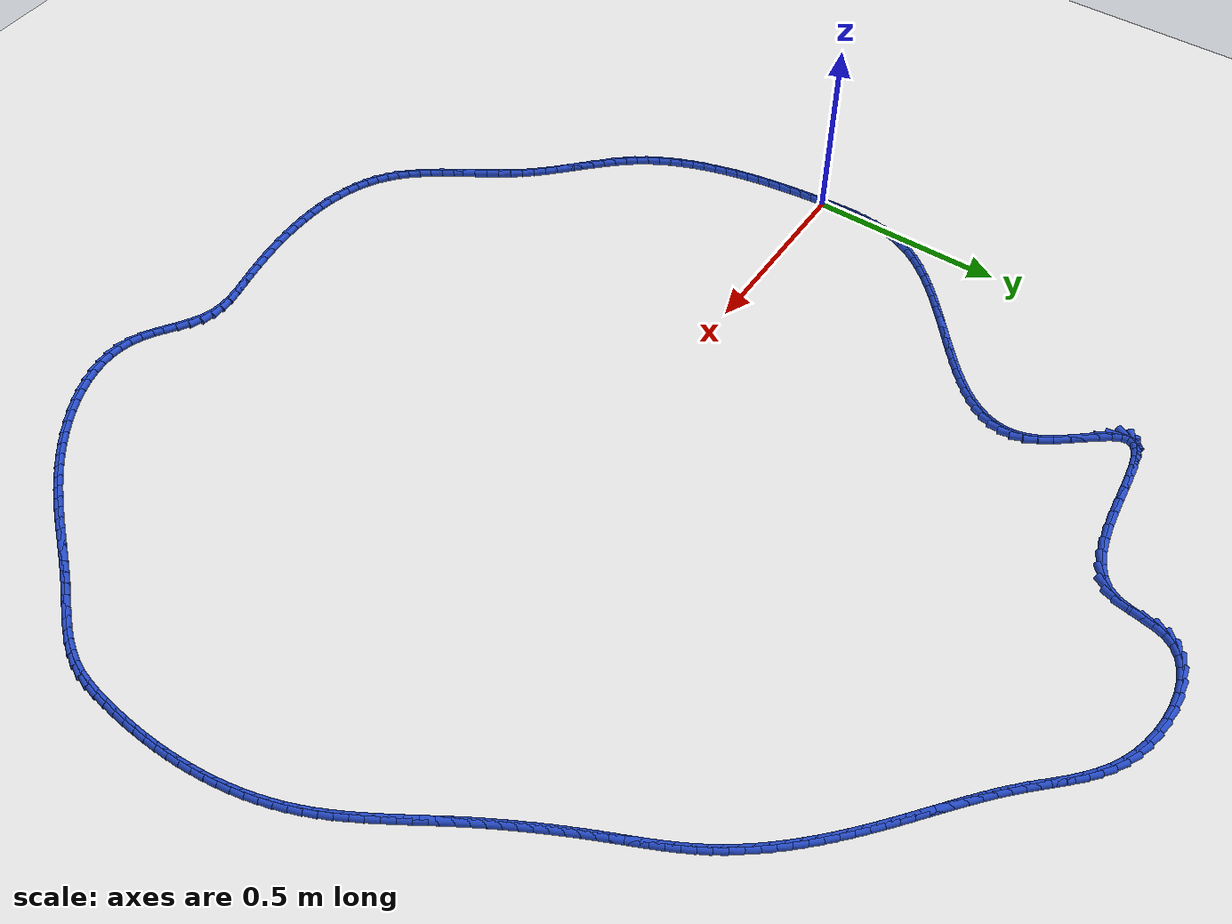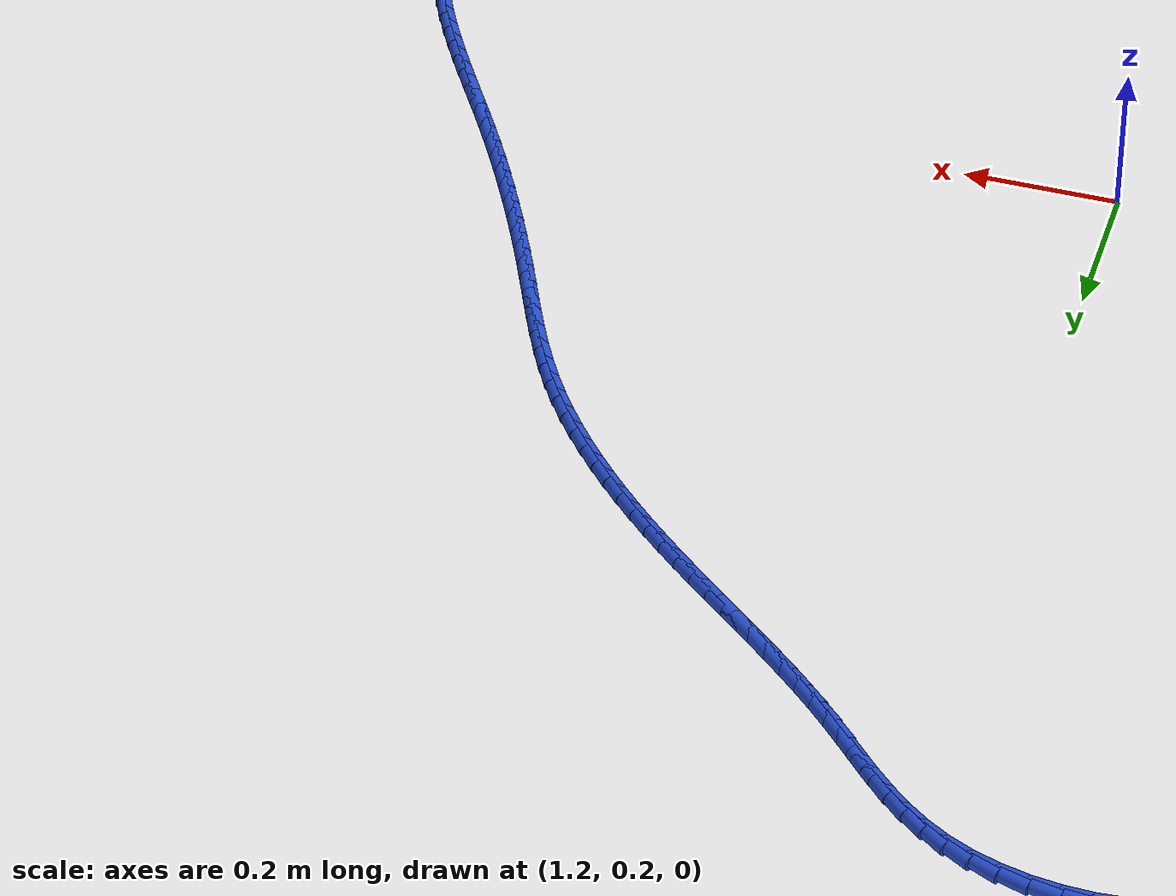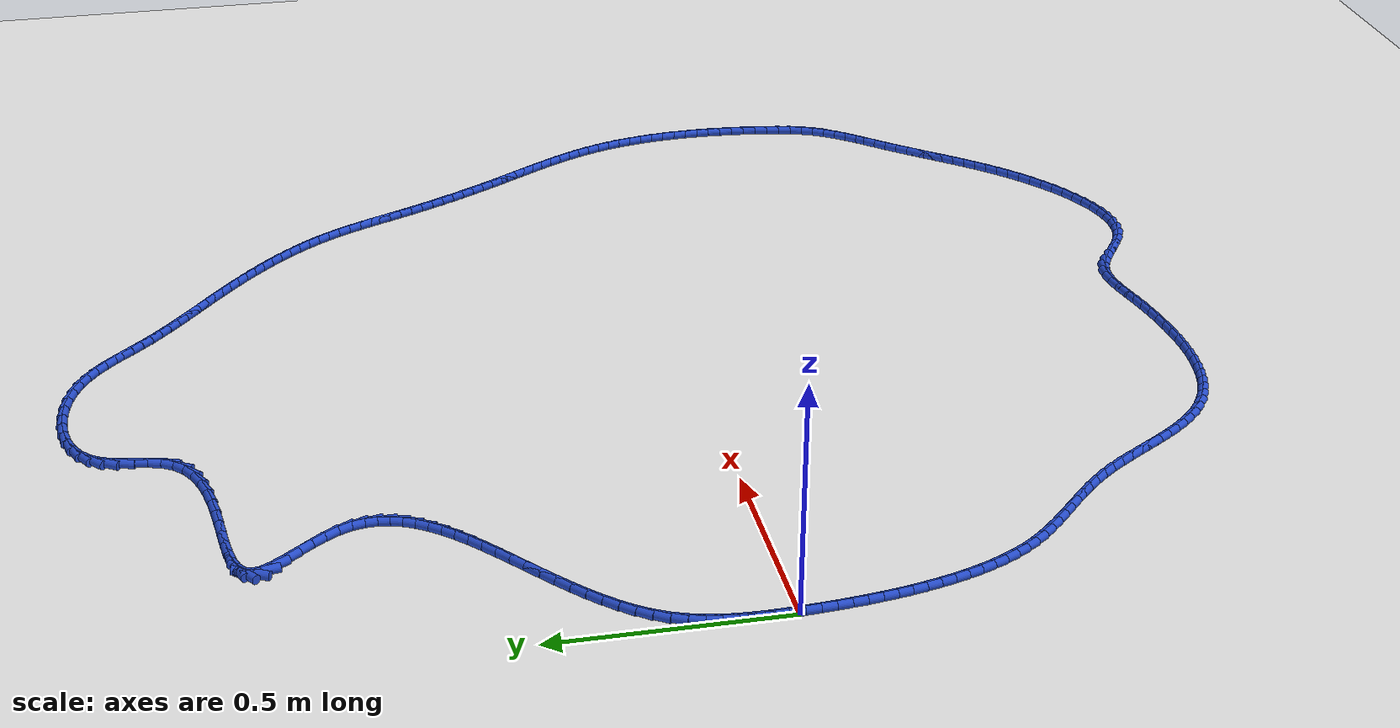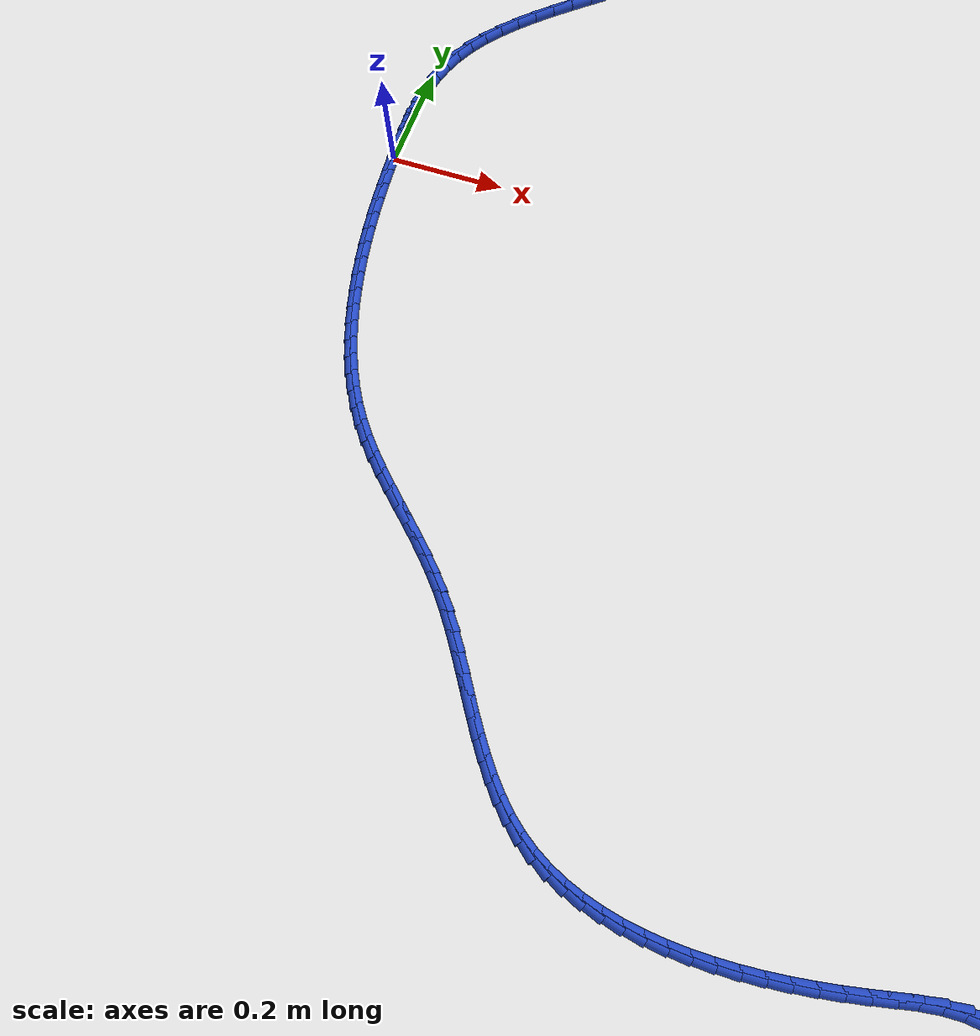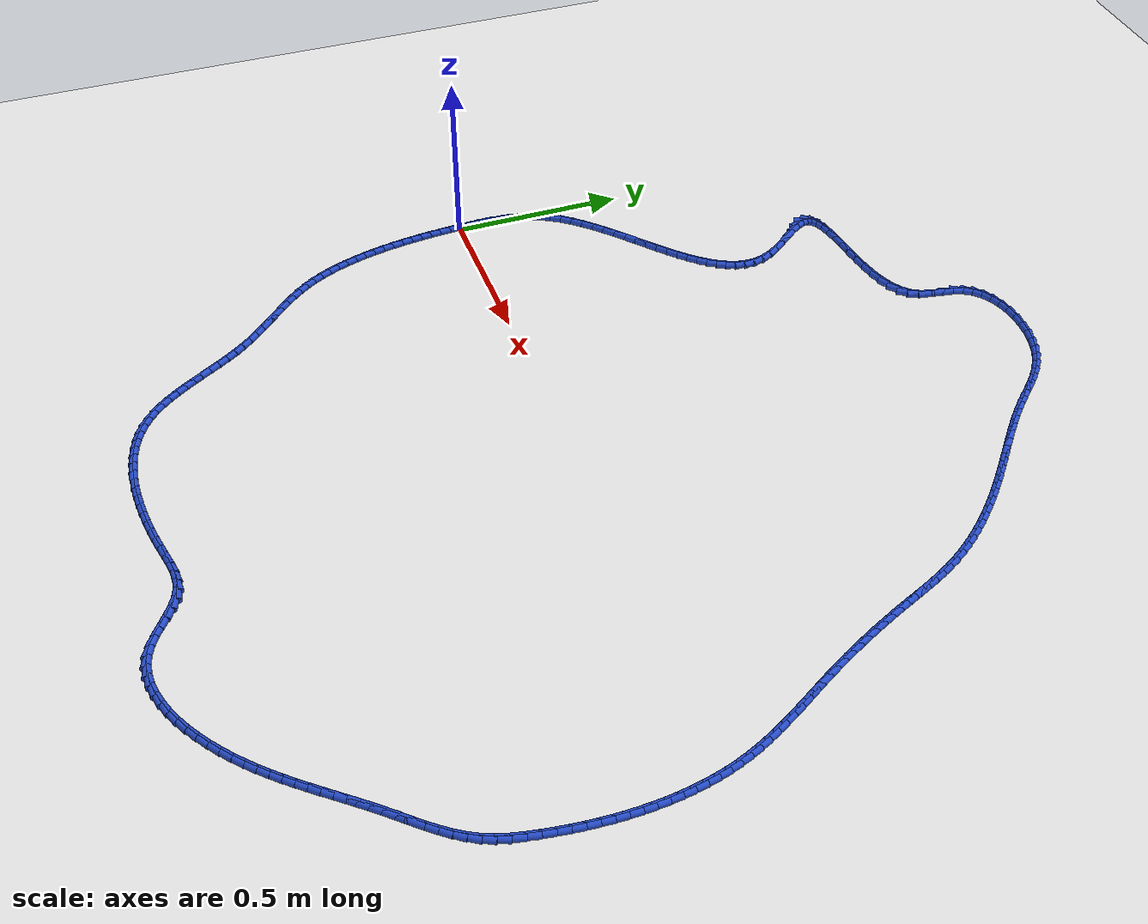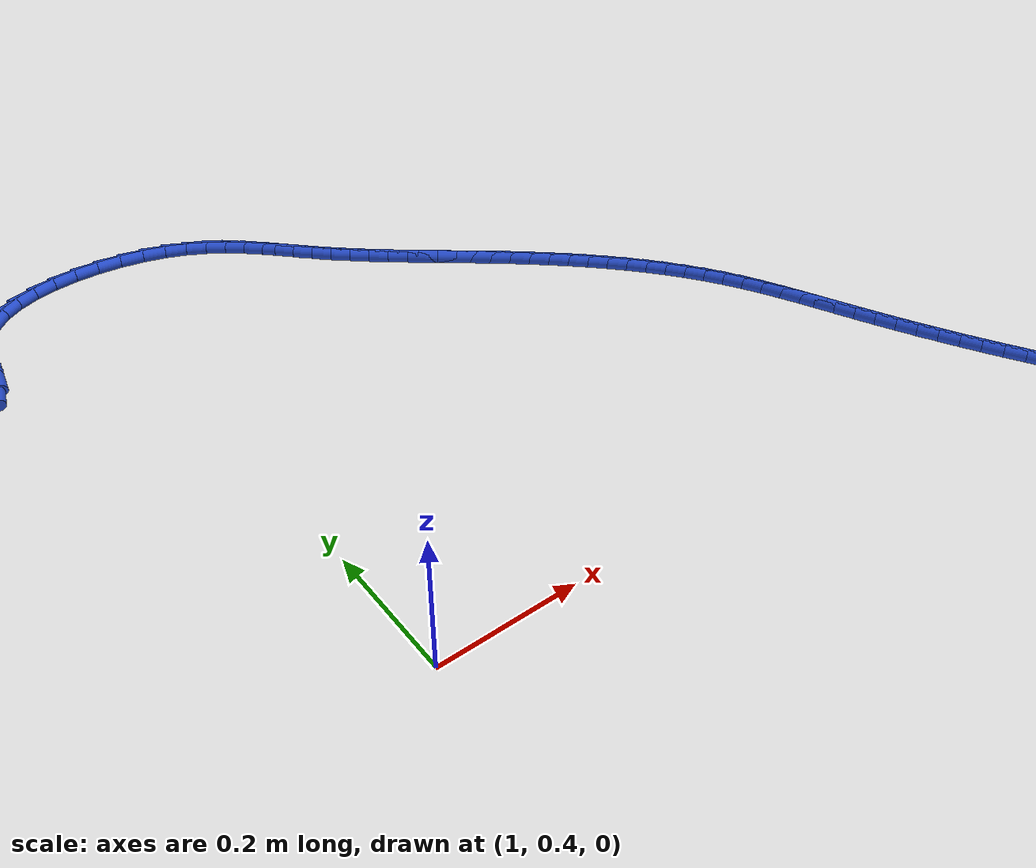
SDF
<sdf version="1.6">
 <world name="default">
  <light name="sun" type="directional">
   <pose>0 0 10 0 -0 0</pose>
   <diffuse>0.8 0.8 0.8 1</diffuse>
   <specular>0.2 0.2 0.2 1</specular>
   <attenuation>
    <range>1000</range>
    <constant>0.9</constant>
    <linear>0.01</linear>
    <quadratic>0.001</quadratic>
   </attenuation>
   <direction>-0.5 0.1 -0.9</direction>
  </light>
  <model name="ground_plane">
   <static>1</static>
   <link name="link">
    <collision name="collision">
     <geometry><plane><normal>0 0 1</normal><size>100 100</size></plane></geometry>
     <surface><friction><ode><mu>100</mu><mu2>50</mu2></ode></friction></surface>
    </collision>
    <visual name="visual">
     <cast_shadows>0</cast_shadows>
     <geometry><plane><normal>0 0 1</normal><size>100 100</size></plane></geometry>
     <material>
      <script><uri>file://media/materials/scripts/gazebo.material</uri><name>Gazebo/WhiteGlow</name></script>
     </material>
    </visual>
   </link>
  </model>
  <gravity>0 0 -9.8</gravity>
  <magnetic_field>6e-06 2.3e-05 -4.2e-05</magnetic_field>
  <atmosphere type="adiabatic"/>
  <physics name="default_physics" default="0" type="ode">
   <max_step_size>0.001</max_step_size>
   <real_time_factor>1</real_time_factor>
   <real_time_update_rate>1000</real_time_update_rate>
  </physics>
  <scene><ambient>0.4 0.4 0.4 1</ambient><background>0.7 0.7 0.7 1</background><shadows>1</shadows></scene>
  <spherical_coordinates>
   <surface_model>EARTH_WGS84</surface_model>
   <latitude_deg>0</latitude_deg>
   <longitude_deg>0</longitude_deg>
   <elevation>0</elevation>
   <heading_deg>0</heading_deg>
  </spherical_coordinates>
  <model name="line">
   <link name="link_0">
    <pose>1.734723475976807e-18 -4.85722573273506e-17 0.01 0 1.57 -1.5189134260214208</pose>
    <collision name="collision">
     <geometry><cylinder><radius>0.01</radius><length>0.08</length></cylinder></geometry>
    </collision>
    <visual name="visual">
     <material>
      <script><name>Gazebo/Blue</name><uri>file://media/materials/scripts/gazebo.material</uri></script>
     </material>
     <geometry><cylinder><radius>0.01</radius><length>0.08</length></cylinder></geometry>
    </visual>
   </link>
   <link name="link_1">
    <pose>-0.0016460797843267311 0.03169835346029947 0.01 0 1.57 -1.5418262945650378</pose>
    <collision name="collision">
     <geometry><cylinder><radius>0.01</radius><length>0.08</length></cylinder></geometry>
    </collision>
    <visual name="visual">
     <material>
      <script><name>Gazebo/Blue</name><uri>file://media/materials/scripts/gazebo.material</uri></script>
     </material>
     <geometry><cylinder><radius>0.01</radius><length>0.08</length></cylinder></geometry>
    </visual>
   </link>
   <link name="link_2">
    <pose>-0.0025672938509750513 0.0634883194280632 0.01 0 1.57 1.5645765763036645</pose>
    <collision name="collision">
     <geometry><cylinder><radius>0.01</radius><length>0.08</length></cylinder></geometry>
    </collision>
    <visual name="visual">
     <material>
      <script><name>Gazebo/Blue</name><uri>file://media/materials/scripts/gazebo.material</uri></script>
     </material>
     <geometry><cylinder><radius>0.01</radius><length>0.08</length></cylinder></geometry>
    </visual>
   </link>
   <link name="link_3">
    <pose>-0.002369825666599471 0.09523648011001434 0.01 0 1.57 1.5166899265524179</pose>
    <collision name="collision">
     <geometry><cylinder><radius>0.01</radius><length>0.08</length></cylinder></geometry>
    </collision>
    <visual name="visual">
     <material>
      <script><name>Gazebo/Blue</name><uri>file://media/materials/scripts/gazebo.material</uri></script>
     </material>
     <geometry><cylinder><radius>0.01</radius><length>0.08</length></cylinder></geometry>
    </visual>
   </link>
   <link name="link_4">
    <pose>-0.0006598586978545061 0.12680941771287624 0.01 0 1.57 1.4556399550820853</pose>
    <collision name="collision">
     <geometry><cylinder><radius>0.01</radius><length>0.08</length></cylinder></geometry>
    </collision>
    <visual name="visual">
     <material>
      <script><name>Gazebo/Blue</name><uri>file://media/materials/scripts/gazebo.material</uri></script>
     </material>
     <geometry><cylinder><radius>0.01</radius><length>0.08</length></cylinder></geometry>
    </visual>
   </link>
   <link name="link_5">
    <pose>0.0029564235886053326 0.158073714443372 0.01 0 1.57 1.381150320873523</pose>
    <collision name="collision">
     <geometry><cylinder><radius>0.01</radius><length>0.08</length></cylinder></geometry>
    </collision>
    <visual name="visual">
     <material>
      <script><name>Gazebo/Blue</name><uri>file://media/materials/scripts/gazebo.material</uri></script>
     </material>
     <geometry><cylinder><radius>0.01</radius><length>0.08</length></cylinder></geometry>
    </visual>
   </link>
   <link name="link_6">
    <pose>0.00887283772612553 0.18889595250822502 0.01 0 1.57 1.293461888868063</pose>
    <collision name="collision">
     <geometry><cylinder><radius>0.01</radius><length>0.08</length></cylinder></geometry>
    </collision>
    <visual name="visual">
     <material>
      <script><name>Gazebo/Blue</name><uri>file://media/materials/scripts/gazebo.material</uri></script>
     </material>
     <geometry><cylinder><radius>0.01</radius><length>0.08</length></cylinder></geometry>
    </visual>
   </link>
   <link name="link_7">
    <pose>0.017483200248051577 0.21914271411415848 0.01 0 1.57 1.1937098474214811</pose>
    <collision name="collision">
     <geometry><cylinder><radius>0.01</radius><length>0.08</length></cylinder></geometry>
    </collision>
    <visual name="visual">
     <material>
      <script><name>Gazebo/Blue</name><uri>file://media/materials/scripts/gazebo.material</uri></script>
     </material>
     <geometry><cylinder><radius>0.01</radius><length>0.08</length></cylinder></geometry>
    </visual>
   </link>
   <link name="link_8">
    <pose>0.02918132768772895 0.24868058146789565 0.01 0 1.57 1.0854017996350127</pose>
    <collision name="collision">
     <geometry><cylinder><radius>0.01</radius><length>0.08</length></cylinder></geometry>
    </collision>
    <visual name="visual">
     <material>
      <script><name>Gazebo/Blue</name><uri>file://media/materials/scripts/gazebo.material</uri></script>
     </material>
     <geometry><cylinder><radius>0.01</radius><length>0.08</length></cylinder></geometry>
    </visual>
   </link>
   <link name="link_9">
    <pose>0.04432294769058389 0.277385789509328 0.01 0 1.57 0.9854817044311218</pose>
    <collision name="collision">
     <geometry><cylinder><radius>0.01</radius><length>0.08</length></cylinder></geometry>
    </collision>
    <visual name="visual">
     <material>
      <script><name>Gazebo/Blue</name><uri>file://media/materials/scripts/gazebo.material</uri></script>
     </material>
     <geometry><cylinder><radius>0.01</radius><length>0.08</length></cylinder></geometry>
    </visual>
   </link>
   <link name="link_10">
    <pose>0.06279357228858395 0.3052537382707447 0.01 0 1.57 0.9032248624812153</pose>
    <collision name="collision">
     <geometry><cylinder><radius>0.01</radius><length>0.08</length></cylinder></geometry>
    </collision>
    <visual name="visual">
     <material>
      <script><name>Gazebo/Blue</name><uri>file://media/materials/scripts/gazebo.material</uri></script>
     </material>
     <geometry><cylinder><radius>0.01</radius><length>0.08</length></cylinder></geometry>
    </visual>
   </link>
   <link name="link_11">
    <pose>0.08416179328791729 0.33236014376482087 0.01 0 1.57 0.8369656892477249</pose>
    <collision name="collision">
     <geometry><cylinder><radius>0.01</radius><length>0.08</length></cylinder></geometry>
    </collision>
    <visual name="visual">
     <material>
      <script><name>Gazebo/Blue</name><uri>file://media/materials/scripts/gazebo.material</uri></script>
     </material>
     <geometry><cylinder><radius>0.01</radius><length>0.08</length></cylinder></geometry>
    </visual>
   </link>
   <link name="link_12">
    <pose>0.10799027667927266 0.35878222376285346 0.01 0 1.57 0.7846928789961841</pose>
    <collision name="collision">
     <geometry><cylinder><radius>0.01</radius><length>0.08</length></cylinder></geometry>
    </collision>
    <visual name="visual">
     <material>
      <script><name>Gazebo/Blue</name><uri>file://media/materials/scripts/gazebo.material</uri></script>
     </material>
     <geometry><cylinder><radius>0.01</radius><length>0.08</length></cylinder></geometry>
    </visual>
   </link>
   <link name="link_13">
    <pose>0.13384168845333874 0.38459719603613923 0.01 0 1.57 0.7446044455101657</pose>
    <collision name="collision">
     <geometry><cylinder><radius>0.01</radius><length>0.08</length></cylinder></geometry>
    </collision>
    <visual name="visual">
     <material>
      <script><name>Gazebo/Blue</name><uri>file://media/materials/scripts/gazebo.material</uri></script>
     </material>
     <geometry><cylinder><radius>0.01</radius><length>0.08</length></cylinder></geometry>
    </visual>
   </link>
   <link name="link_14">
    <pose>0.16127869460080424 0.40988227835597485 0.01 0 1.57 0.7152584562376902</pose>
    <collision name="collision">
     <geometry><cylinder><radius>0.01</radius><length>0.08</length></cylinder></geometry>
    </collision>
    <visual name="visual">
     <material>
      <script><name>Gazebo/Blue</name><uri>file://media/materials/scripts/gazebo.material</uri></script>
     </material>
     <geometry><cylinder><radius>0.01</radius><length>0.08</length></cylinder></geometry>
    </visual>
   </link>
   <link name="link_15">
    <pose>0.1898639611123579 0.43471468849365724 0.01 0 1.57 0.6956131613511655</pose>
    <collision name="collision">
     <geometry><cylinder><radius>0.01</radius><length>0.08</length></cylinder></geometry>
    </collision>
    <visual name="visual">
     <material>
      <script><name>Gazebo/Blue</name><uri>file://media/materials/scripts/gazebo.material</uri></script>
     </material>
     <geometry><cylinder><radius>0.01</radius><length>0.08</length></cylinder></geometry>
    </visual>
   </link>
   <link name="link_16">
    <pose>0.2191601539786885 0.45917164422048323 0.01 0 1.57 0.6850253288112776</pose>
    <collision name="collision">
     <geometry><cylinder><radius>0.01</radius><length>0.08</length></cylinder></geometry>
    </collision>
    <visual name="visual">
     <material>
      <script><name>Gazebo/Blue</name><uri>file://media/materials/scripts/gazebo.material</uri></script>
     </material>
     <geometry><cylinder><radius>0.01</radius><length>0.08</length></cylinder></geometry>
    </visual>
   </link>
   <link name="link_17">
    <pose>0.24872993919048458 0.4833303633077494 0.01 0 1.57 0.6832435721577305</pose>
    <collision name="collision">
     <geometry><cylinder><radius>0.01</radius><length>0.08</length></cylinder></geometry>
    </collision>
    <visual name="visual">
     <material>
      <script><name>Gazebo/Blue</name><uri>file://media/materials/scripts/gazebo.material</uri></script>
     </material>
     <geometry><cylinder><radius>0.01</radius><length>0.08</length></cylinder></geometry>
    </visual>
   </link>
   <link name="link_18">
    <pose>0.27813598273843515 0.5072680635267528 0.01 0 1.57 0.6904153159585457</pose>
    <collision name="collision">
     <geometry><cylinder><radius>0.01</radius><length>0.08</length></cylinder></geometry>
    </collision>
    <visual name="visual">
     <material>
      <script><name>Gazebo/Blue</name><uri>file://media/materials/scripts/gazebo.material</uri></script>
     </material>
     <geometry><cylinder><radius>0.01</radius><length>0.08</length></cylinder></geometry>
    </visual>
   </link>
   <link name="link_19">
    <pose>0.3069409506132286 0.53106196264879 0.01 0 1.57 0.7071172337519179</pose>
    <collision name="collision">
     <geometry><cylinder><radius>0.01</radius><length>0.08</length></cylinder></geometry>
    </collision>
    <visual name="visual">
     <material>
      <script><name>Gazebo/Blue</name><uri>file://media/materials/scripts/gazebo.material</uri></script>
     </material>
     <geometry><cylinder><radius>0.01</radius><length>0.08</length></cylinder></geometry>
    </visual>
   </link>
   <link name="link_20">
    <pose>0.33470750880555394 0.554789278445158 0.01 0 1.57 0.7344144549488046</pose>
    <collision name="collision">
     <geometry><cylinder><radius>0.01</radius><length>0.08</length></cylinder></geometry>
    </collision>
    <visual name="visual">
     <material>
      <script><name>Gazebo/Blue</name><uri>file://media/materials/scripts/gazebo.material</uri></script>
     </material>
     <geometry><cylinder><radius>0.01</radius><length>0.08</length></cylinder></geometry>
    </visual>
   </link>
   <link name="link_21">
    <pose>0.3609983233060997 0.5785272286871536 0.01 0 1.57 0.7739485845781411</pose>
    <collision name="collision">
     <geometry><cylinder><radius>0.01</radius><length>0.08</length></cylinder></geometry>
    </collision>
    <visual name="visual">
     <material>
      <script><name>Gazebo/Blue</name><uri>file://media/materials/scripts/gazebo.material</uri></script>
     </material>
     <geometry><cylinder><radius>0.01</radius><length>0.08</length></cylinder></geometry>
    </visual>
   </link>
   <link name="link_22">
    <pose>0.38537606010555475 0.6023530311460733 0.01 0 1.57 0.8280412291195116</pose>
    <collision name="collision">
     <geometry><cylinder><radius>0.01</radius><length>0.08</length></cylinder></geometry>
    </collision>
    <visual name="visual">
     <material>
      <script><name>Gazebo/Blue</name><uri>file://media/materials/scripts/gazebo.material</uri></script>
     </material>
     <geometry><cylinder><radius>0.01</radius><length>0.08</length></cylinder></geometry>
    </visual>
   </link>
   <link name="link_23">
    <pose>0.40740338519460767 0.6263439035932142 0.01 0 1.57 0.8997638710351674</pose>
    <collision name="collision">
     <geometry><cylinder><radius>0.01</radius><length>0.08</length></cylinder></geometry>
    </collision>
    <visual name="visual">
     <material>
      <script><name>Gazebo/Blue</name><uri>file://media/materials/scripts/gazebo.material</uri></script>
     </material>
     <geometry><cylinder><radius>0.01</radius><length>0.08</length></cylinder></geometry>
    </visual>
   </link>
   <link name="link_24">
    <pose>0.42664296456394735 0.650577063799873 0.01 0 1.57 0.9928403407481277</pose>
    <collision name="collision">
     <geometry><cylinder><radius>0.01</radius><length>0.08</length></cylinder></geometry>
    </collision>
    <visual name="visual">
     <material>
      <script><name>Gazebo/Blue</name><uri>file://media/materials/scripts/gazebo.material</uri></script>
     </material>
     <geometry><cylinder><radius>0.01</radius><length>0.08</length></cylinder></geometry>
    </visual>
   </link>
   <link name="link_25">
    <pose>0.44265746420426233 0.6751297295373464 0.01 0 1.57 1.1110878754475098</pose>
    <collision name="collision">
     <geometry><cylinder><radius>0.01</radius><length>0.08</length></cylinder></geometry>
    </collision>
    <visual name="visual">
     <material>
      <script><name>Gazebo/Blue</name><uri>file://media/materials/scripts/gazebo.material</uri></script>
     </material>
     <geometry><cylinder><radius>0.01</radius><length>0.08</length></cylinder></geometry>
    </visual>
   </link>
   <link name="link_26">
    <pose>0.45500955010624133 0.7000791185769313 0.01 0 1.57 1.2569289182996217</pose>
    <collision name="collision">
     <geometry><cylinder><radius>0.01</radius><length>0.08</length></cylinder></geometry>
    </collision>
    <visual name="visual">
     <material>
      <script><name>Gazebo/Blue</name><uri>file://media/materials/scripts/gazebo.material</uri></script>
     </material>
     <geometry><cylinder><radius>0.01</radius><length>0.08</length></cylinder></geometry>
    </visual>
   </link>
   <link name="link_27">
    <pose>0.4632618882605733 0.7255024486899246 0.01 0 1.57 1.4287251512366161</pose>
    <collision name="collision">
     <geometry><cylinder><radius>0.01</radius><length>0.08</length></cylinder></geometry>
    </collision>
    <visual name="visual">
     <material>
      <script><name>Gazebo/Blue</name><uri>file://media/materials/scripts/gazebo.material</uri></script>
     </material>
     <geometry><cylinder><radius>0.01</radius><length>0.08</length></cylinder></geometry>
    </visual>
   </link>
   <link name="link_28">
    <pose>0.46697714465794665 0.7514769376476229 0.01 0 1.57 -1.5234999055666298</pose>
    <collision name="collision">
     <geometry><cylinder><radius>0.01</radius><length>0.08</length></cylinder></geometry>
    </collision>
    <visual name="visual">
     <material>
      <script><name>Gazebo/Blue</name><uri>file://media/materials/scripts/gazebo.material</uri></script>
     </material>
     <geometry><cylinder><radius>0.01</radius><length>0.08</length></cylinder></geometry>
    </visual>
   </link>
   <link name="link_29">
    <pose>0.46571798528905034 0.778079803221323 0.01 0 1.57 -1.3312084464958525</pose>
    <collision name="collision">
     <geometry><cylinder><radius>0.01</radius><length>0.08</length></cylinder></geometry>
    </collision>
    <visual name="visual">
     <material>
      <script><name>Gazebo/Blue</name><uri>file://media/materials/scripts/gazebo.material</uri></script>
     </material>
     <geometry><cylinder><radius>0.01</radius><length>0.08</length></cylinder></geometry>
    </visual>
   </link>
   <link name="link_30">
    <pose>0.4590470761445731 0.8053882631823218 0.01 0 1.57 -1.1515338383840577</pose>
    <collision name="collision">
     <geometry><cylinder><radius>0.01</radius><length>0.08</length></cylinder></geometry>
    </collision>
    <visual name="visual">
     <material>
      <script><name>Gazebo/Blue</name><uri>file://media/materials/scripts/gazebo.material</uri></script>
     </material>
     <geometry><cylinder><radius>0.01</radius><length>0.08</length></cylinder></geometry>
    </visual>
   </link>
   <link name="link_31">
    <pose>0.44652713254071225 0.8334795214001698 0.01 0 1.57 -1.0059503788455562</pose>
    <collision name="collision">
     <geometry><cylinder><radius>0.01</radius><length>0.08</length></cylinder></geometry>
    </collision>
    <visual name="visual">
     <material>
      <script><name>Gazebo/Blue</name><uri>file://media/materials/scripts/gazebo.material</uri></script>
     </material>
     <geometry><cylinder><radius>0.01</radius><length>0.08</length></cylinder></geometry>
    </visual>
   </link>
   <link name="link_32">
    <pose>0.42827997343888735 0.8622732057305147 0.01 0 1.57 -0.9216304899793426</pose>
    <collision name="collision">
     <geometry><cylinder><radius>0.01</radius><length>0.08</length></cylinder></geometry>
    </collision>
    <visual name="visual">
     <material>
      <script><name>Gazebo/Blue</name><uri>file://media/materials/scripts/gazebo.material</uri></script>
     </material>
     <geometry><cylinder><radius>0.01</radius><length>0.08</length></cylinder></geometry>
    </visual>
   </link>
   <link name="link_33">
    <pose>0.40637277105334624 0.8911406717831823 0.01 0 1.57 -0.8848567821568042</pose>
    <collision name="collision">
     <geometry><cylinder><radius>0.01</radius><length>0.08</length></cylinder></geometry>
    </collision>
    <visual name="visual">
     <material>
      <script><name>Gazebo/Blue</name><uri>file://media/materials/scripts/gazebo.material</uri></script>
     </material>
     <geometry><cylinder><radius>0.01</radius><length>0.08</length></cylinder></geometry>
    </visual>
   </link>
   <link name="link_34">
    <pose>0.38329552865643496 0.9193341057916969 0.01 0 1.57 -0.8883591014984118</pose>
    <collision name="collision">
     <geometry><cylinder><radius>0.01</radius><length>0.08</length></cylinder></geometry>
    </collision>
    <visual name="visual">
     <material>
      <script><name>Gazebo/Blue</name><uri>file://media/materials/scripts/gazebo.material</uri></script>
     </material>
     <geometry><cylinder><radius>0.01</radius><length>0.08</length></cylinder></geometry>
    </visual>
   </link>
   <link name="link_35">
    <pose>0.36153824952049896 0.946105693989582 0.01 0 1.57 -0.9405393700569313</pose>
    <collision name="collision">
     <geometry><cylinder><radius>0.01</radius><length>0.08</length></cylinder></geometry>
    </collision>
    <visual name="visual">
     <material>
      <script><name>Gazebo/Blue</name><uri>file://media/materials/scripts/gazebo.material</uri></script>
     </material>
     <geometry><cylinder><radius>0.01</radius><length>0.08</length></cylinder></geometry>
    </visual>
   </link>
   <link name="link_36">
    <pose>0.34359093691788434 0.9707076226103615 0.01 0 1.57 -1.0778888052492228</pose>
    <collision name="collision">
     <geometry><cylinder><radius>0.01</radius><length>0.08</length></cylinder></geometry>
    </collision>
    <visual name="visual">
     <material>
      <script><name>Gazebo/Blue</name><uri>file://media/materials/scripts/gazebo.material</uri></script>
     </material>
     <geometry><cylinder><radius>0.01</radius><length>0.08</length></cylinder></geometry>
    </visual>
   </link>
   <link name="link_37">
    <pose>0.33194359412093677 0.9923920778875597 0.01 0 1.57 -1.4119749061984015</pose>
    <collision name="collision">
     <geometry><cylinder><radius>0.01</radius><length>0.08</length></cylinder></geometry>
    </collision>
    <visual name="visual">
     <material>
      <script><name>Gazebo/Blue</name><uri>file://media/materials/scripts/gazebo.material</uri></script>
     </material>
     <geometry><cylinder><radius>0.01</radius><length>0.08</length></cylinder></geometry>
    </visual>
   </link>
   <link name="link_38">
    <pose>0.32905564551787486 1.0104225523310293 0.01 0 1.57 1.1199391585044085</pose>
    <collision name="collision">
     <geometry><cylinder><radius>0.01</radius><length>0.08</length></cylinder></geometry>
    </collision>
    <visual name="visual">
     <material>
      <script><name>Gazebo/Blue</name><uri>file://media/materials/scripts/gazebo.material</uri></script>
     </material>
     <geometry><cylinder><radius>0.01</radius><length>0.08</length></cylinder></geometry>
    </visual>
   </link>
   <link name="link_39">
    <pose>0.33592121875034453 1.024604319172656 0.01 0 1.57 0.6122443756255788</pose>
    <collision name="collision">
     <geometry><cylinder><radius>0.01</radius><length>0.08</length></cylinder></geometry>
    </collision>
    <visual name="visual">
     <material>
      <script><name>Gazebo/Blue</name><uri>file://media/materials/scripts/gazebo.material</uri></script>
     </material>
     <geometry><cylinder><radius>0.01</radius><length>0.08</length></cylinder></geometry>
    </visual>
   </link>
   <link name="link_40">
    <pose>0.35145346962300356 1.035512072873852 0.01 0 1.57 0.3456996774239005</pose>
    <collision name="collision">
     <geometry><cylinder><radius>0.01</radius><length>0.08</length></cylinder></geometry>
    </collision>
    <visual name="visual">
     <material>
      <script><name>Gazebo/Blue</name><uri>file://media/materials/scripts/gazebo.material</uri></script>
     </material>
     <geometry><cylinder><radius>0.01</radius><length>0.08</length></cylinder></geometry>
    </visual>
   </link>
   <link name="link_41">
    <pose>0.3744070707561347 1.0437791056744408 0.01 0 1.57 0.21166902380520375</pose>
    <collision name="collision">
     <geometry><cylinder><radius>0.01</radius><length>0.08</length></cylinder></geometry>
    </collision>
    <visual name="visual">
     <material>
      <script><name>Gazebo/Blue</name><uri>file://media/materials/scripts/gazebo.material</uri></script>
     </material>
     <geometry><cylinder><radius>0.01</radius><length>0.08</length></cylinder></geometry>
    </visual>
   </link>
   <link name="link_42">
    <pose>0.40353669477002047 1.0500387098142452 0.01 0 1.57 0.1424640506332432</pose>
    <collision name="collision">
     <geometry><cylinder><radius>0.01</radius><length>0.08</length></cylinder></geometry>
    </collision>
    <visual name="visual">
     <material>
      <script><name>Gazebo/Blue</name><uri>file://media/materials/scripts/gazebo.material</uri></script>
     </material>
     <geometry><cylinder><radius>0.01</radius><length>0.08</length></cylinder></geometry>
    </visual>
   </link>
   <link name="link_43">
    <pose>0.437597014284944 1.0549241775330884 0.01 0 1.57 0.10936576256194688</pose>
    <collision name="collision">
     <geometry><cylinder><radius>0.01</radius><length>0.08</length></cylinder></geometry>
    </collision>
    <visual name="visual">
     <material>
      <script><name>Gazebo/Blue</name><uri>file://media/materials/scripts/gazebo.material</uri></script>
     </material>
     <geometry><cylinder><radius>0.01</radius><length>0.08</length></cylinder></geometry>
    </visual>
   </link>
   <link name="link_44">
    <pose>0.47534270192118766 1.059068801070793 0.01 0 1.57 0.10012440549877785</pose>
    <collision name="collision">
     <geometry><cylinder><radius>0.01</radius><length>0.08</length></cylinder></geometry>
    </collision>
    <visual name="visual">
     <material>
      <script><name>Gazebo/Blue</name><uri>file://media/materials/scripts/gazebo.material</uri></script>
     </material>
     <geometry><cylinder><radius>0.01</radius><length>0.08</length></cylinder></geometry>
    </visual>
   </link>
   <link name="link_45">
    <pose>0.5155284302990344 1.063105872667182 0.01 0 1.57 0.10982129104937971</pose>
    <collision name="collision">
     <geometry><cylinder><radius>0.01</radius><length>0.08</length></cylinder></geometry>
    </collision>
    <visual name="visual">
     <material>
      <script><name>Gazebo/Blue</name><uri>file://media/materials/scripts/gazebo.material</uri></script>
     </material>
     <geometry><cylinder><radius>0.01</radius><length>0.08</length></cylinder></geometry>
    </visual>
   </link>
   <link name="link_46">
    <pose>0.5569088720387666 1.0676686845620786 0.01 0 1.57 0.13756899999003805</pose>
    <collision name="collision">
     <geometry><cylinder><radius>0.01</radius><length>0.08</length></cylinder></geometry>
    </collision>
    <visual name="visual">
     <material>
      <script><name>Gazebo/Blue</name><uri>file://media/materials/scripts/gazebo.material</uri></script>
     </material>
     <geometry><cylinder><radius>0.01</radius><length>0.08</length></cylinder></geometry>
    </visual>
   </link>
   <link name="link_47">
    <pose>0.5982386997606676 1.0733905289953056 0.01 0 1.57 0.18553653587266689</pose>
    <collision name="collision">
     <geometry><cylinder><radius>0.01</radius><length>0.08</length></cylinder></geometry>
    </collision>
    <visual name="visual">
     <material>
      <script><name>Gazebo/Blue</name><uri>file://media/materials/scripts/gazebo.material</uri></script>
     </material>
     <geometry><cylinder><radius>0.01</radius><length>0.08</length></cylinder></geometry>
    </visual>
   </link>
   <link name="link_48">
    <pose>0.6382725860850198 1.080904698206686 0.01 0 1.57 0.2591514601777915</pose>
    <collision name="collision">
     <geometry><cylinder><radius>0.01</radius><length>0.08</length></cylinder></geometry>
    </collision>
    <visual name="visual">
     <material>
      <script><name>Gazebo/Blue</name><uri>file://media/materials/scripts/gazebo.material</uri></script>
     </material>
     <geometry><cylinder><radius>0.01</radius><length>0.08</length></cylinder></geometry>
    </visual>
   </link>
   <link name="link_49">
    <pose>0.6757652036321055 1.090844484436043 0.01 0 1.57 0.3680739921741338</pose>
    <collision name="collision">
     <geometry><cylinder><radius>0.01</radius><length>0.08</length></cylinder></geometry>
    </collision>
    <visual name="visual">
     <material>
      <script><name>Gazebo/Blue</name><uri>file://media/materials/scripts/gazebo.material</uri></script>
     </material>
     <geometry><cylinder><radius>0.01</radius><length>0.08</length></cylinder></geometry>
    </visual>
   </link>
   <link name="link_50">
    <pose>0.7094712250222078 1.103843179923199 0.01 0 1.57 0.527146053106423</pose>
    <collision name="collision">
     <geometry><cylinder><radius>0.01</radius><length>0.08</length></cylinder></geometry>
    </collision>
    <visual name="visual">
     <material>
      <script><name>Gazebo/Blue</name><uri>file://media/materials/scripts/gazebo.material</uri></script>
     </material>
     <geometry><cylinder><radius>0.01</radius><length>0.08</length></cylinder></geometry>
    </visual>
   </link>
   <link name="link_51">
    <pose>0.7381453228756094 1.120534076907977 0.01 0 1.57 0.753610826074289</pose>
    <collision name="collision">
     <geometry><cylinder><radius>0.01</radius><length>0.08</length></cylinder></geometry>
    </collision>
    <visual name="visual">
     <material>
      <script><name>Gazebo/Blue</name><uri>file://media/materials/scripts/gazebo.material</uri></script>
     </material>
     <geometry><cylinder><radius>0.01</radius><length>0.08</length></cylinder></geometry>
    </visual>
   </link>
   <link name="link_52">
    <pose>0.7605421698125935 1.141550467630201 0.01 0 1.57 1.0469563369030594</pose>
    <collision name="collision">
     <geometry><cylinder><radius>0.01</radius><length>0.08</length></cylinder></geometry>
    </collision>
    <visual name="visual">
     <material>
      <script><name>Gazebo/Blue</name><uri>file://media/materials/scripts/gazebo.material</uri></script>
     </material>
     <geometry><cylinder><radius>0.01</radius><length>0.08</length></cylinder></geometry>
    </visual>
   </link>
   <link name="link_53">
    <pose>0.7755125520495563 1.1674654920246001 0.01 0 1.57 1.2920843228856336</pose>
    <collision name="collision">
     <geometry><cylinder><radius>0.01</radius><length>0.08</length></cylinder></geometry>
    </collision>
    <visual name="visual">
     <material>
      <script><name>Gazebo/Blue</name><uri>file://media/materials/scripts/gazebo.material</uri></script>
     </material>
     <geometry><cylinder><radius>0.01</radius><length>0.08</length></cylinder></geometry>
    </visual>
   </link>
   <link name="link_54">
    <pose>0.7841012767249345 1.19747917091251 0.01 0 1.57 1.4022214852029578</pose>
    <collision name="collision">
     <geometry><cylinder><radius>0.01</radius><length>0.08</length></cylinder></geometry>
    </collision>
    <visual name="visual">
     <material>
      <script><name>Gazebo/Blue</name><uri>file://media/materials/scripts/gazebo.material</uri></script>
     </material>
     <geometry><cylinder><radius>0.01</radius><length>0.08</length></cylinder></geometry>
    </visual>
   </link>
   <link name="link_55">
    <pose>0.7895379936345978 1.229424150181623 0.01 0 1.57 1.395408541677641</pose>
    <collision name="collision">
     <geometry><cylinder><radius>0.01</radius><length>0.08</length></cylinder></geometry>
    </collision>
    <visual name="visual">
     <material>
      <script><name>Gazebo/Blue</name><uri>file://media/materials/scripts/gazebo.material</uri></script>
     </material>
     <geometry><cylinder><radius>0.01</radius><length>0.08</length></cylinder></geometry>
    </visual>
   </link>
   <link name="link_56">
    <pose>0.7951466305074962 1.2610740722568186 0.01 0 1.57 1.2678543479114326</pose>
    <collision name="collision">
     <geometry><cylinder><radius>0.01</radius><length>0.08</length></cylinder></geometry>
    </collision>
    <visual name="visual">
     <material>
      <script><name>Gazebo/Blue</name><uri>file://media/materials/scripts/gazebo.material</uri></script>
     </material>
     <geometry><cylinder><radius>0.01</radius><length>0.08</length></cylinder></geometry>
    </visual>
   </link>
   <link name="link_57">
    <pose>0.8042511150725808 1.2902025795629755 0.01 0 1.57 1.0161365986097153</pose>
    <collision name="collision">
     <geometry><cylinder><radius>0.01</radius><length>0.08</length></cylinder></geometry>
    </collision>
    <visual name="visual">
     <material>
      <script><name>Gazebo/Blue</name><uri>file://media/materials/scripts/gazebo.material</uri></script>
     </material>
     <geometry><cylinder><radius>0.01</radius><length>0.08</length></cylinder></geometry>
    </visual>
   </link>
   <link name="link_58">
    <pose>0.8195670444298113 1.3149242350780586 0.01 0 1.57 0.7529976357269617</pose>
    <collision name="collision">
     <geometry><cylinder><radius>0.01</radius><length>0.08</length></cylinder></geometry>
    </collision>
    <visual name="visual">
     <material>
      <script><name>Gazebo/Blue</name><uri>file://media/materials/scripts/gazebo.material</uri></script>
     </material>
     <geometry><cylinder><radius>0.01</radius><length>0.08</length></cylinder></geometry>
    </visual>
   </link>
   <link name="link_59">
    <pose>0.8409445430025707 1.3349594695157612 0.01 0 1.57 0.5313029907111606</pose>
    <collision name="collision">
     <geometry><cylinder><radius>0.01</radius><length>0.08</length></cylinder></geometry>
    </collision>
    <visual name="visual">
     <material>
      <script><name>Gazebo/Blue</name><uri>file://media/materials/scripts/gazebo.material</uri></script>
     </material>
     <geometry><cylinder><radius>0.01</radius><length>0.08</length></cylinder></geometry>
    </visual>
   </link>
   <link name="link_60">
    <pose>0.8673908046752399 1.3505011085866325 0.01 0 1.57 0.35287352331071287</pose>
    <collision name="collision">
     <geometry><cylinder><radius>0.01</radius><length>0.08</length></cylinder></geometry>
    </collision>
    <visual name="visual">
     <material>
      <script><name>Gazebo/Blue</name><uri>file://media/materials/scripts/gazebo.material</uri></script>
     </material>
     <geometry><cylinder><radius>0.01</radius><length>0.08</length></cylinder></geometry>
    </visual>
   </link>
   <link name="link_61">
    <pose>0.8979129075120189 1.3617420429091482 0.01 0 1.57 0.2091591169639746</pose>
    <collision name="collision">
     <geometry><cylinder><radius>0.01</radius><length>0.08</length></cylinder></geometry>
    </collision>
    <visual name="visual">
     <material>
      <script><name>Gazebo/Blue</name><uri>file://media/materials/scripts/gazebo.material</uri></script>
     </material>
     <geometry><cylinder><radius>0.01</radius><length>0.08</length></cylinder></geometry>
    </visual>
   </link>
   <link name="link_62">
    <pose>0.9315179295771093 1.3688751631017848 0.01 0 1.57 0.08991504490829086</pose>
    <collision name="collision">
     <geometry><cylinder><radius>0.01</radius><length>0.08</length></cylinder></geometry>
    </collision>
    <visual name="visual">
     <material>
      <script><name>Gazebo/Blue</name><uri>file://media/materials/scripts/gazebo.material</uri></script>
     </material>
     <geometry><cylinder><radius>0.01</radius><length>0.08</length></cylinder></geometry>
    </visual>
   </link>
   <link name="link_63">
    <pose>0.9672129489347117 1.3720933597830174 0.01 0 1.57 -0.013693287224428823</pose>
    <collision name="collision">
     <geometry><cylinder><radius>0.01</radius><length>0.08</length></cylinder></geometry>
    </collision>
    <visual name="visual">
     <material>
      <script><name>Gazebo/Blue</name><uri>file://media/materials/scripts/gazebo.material</uri></script>
     </material>
     <geometry><cylinder><radius>0.01</radius><length>0.08</length></cylinder></geometry>
    </visual>
   </link>
   <link name="link_64">
    <pose>1.0040050436490255 1.371589523571322 0.01 0 1.57 -0.108873696835155</pose>
    <collision name="collision">
     <geometry><cylinder><radius>0.01</radius><length>0.08</length></cylinder></geometry>
    </collision>
    <visual name="visual">
     <material>
      <script><name>Gazebo/Blue</name><uri>file://media/materials/scripts/gazebo.material</uri></script>
     </material>
     <geometry><cylinder><radius>0.01</radius><length>0.08</length></cylinder></geometry>
    </visual>
   </link>
   <link name="link_65">
    <pose>1.040901291784253 1.367556545085175 0.01 0 1.57 -0.2018706710001404</pose>
    <collision name="collision">
     <geometry><cylinder><radius>0.01</radius><length>0.08</length></cylinder></geometry>
    </collision>
    <visual name="visual">
     <material>
      <script><name>Gazebo/Blue</name><uri>file://media/materials/scripts/gazebo.material</uri></script>
     </material>
     <geometry><cylinder><radius>0.01</radius><length>0.08</length></cylinder></geometry>
    </visual>
   </link>
   <link name="link_66">
    <pose>1.0769087714045944 1.3601873149430515 0.01 0 1.57 -0.29882945125309424</pose>
    <collision name="collision">
     <geometry><cylinder><radius>0.01</radius><length>0.08</length></cylinder></geometry>
    </collision>
    <visual name="visual">
     <material>
      <script><name>Gazebo/Blue</name><uri>file://media/materials/scripts/gazebo.material</uri></script>
     </material>
     <geometry><cylinder><radius>0.01</radius><length>0.08</length></cylinder></geometry>
    </visual>
   </link>
   <link name="link_67">
    <pose>1.111034560574249 1.3496747237634277 0.01 0 1.57 -0.40575146708771503</pose>
    <collision name="collision">
     <geometry><cylinder><radius>0.01</radius><length>0.08</length></cylinder></geometry>
    </collision>
    <visual name="visual">
     <material>
      <script><name>Gazebo/Blue</name><uri>file://media/materials/scripts/gazebo.material</uri></script>
     </material>
     <geometry><cylinder><radius>0.01</radius><length>0.08</length></cylinder></geometry>
    </visual>
   </link>
   <link name="link_68">
    <pose>1.142348189048469 1.3362227213578386 0.01 0 1.57 -0.5140036319667555</pose>
    <collision name="collision">
     <geometry><cylinder><radius>0.01</radius><length>0.08</length></cylinder></geometry>
    </collision>
    <visual name="visual">
     <material>
      <script><name>Gazebo/Blue</name><uri>file://media/materials/scripts/gazebo.material</uri></script>
     </material>
     <geometry><cylinder><radius>0.01</radius><length>0.08</length></cylinder></geometry>
    </visual>
   </link>
   <link name="link_69">
    <pose>1.1707552788197175 1.320183316066111 0.01 0 1.57 -0.6098756465946839</pose>
    <collision name="collision">
     <geometry><cylinder><radius>0.01</radius><length>0.08</length></cylinder></geometry>
    </collision>
    <visual name="visual">
     <material>
      <script><name>Gazebo/Blue</name><uri>file://media/materials/scripts/gazebo.material</uri></script>
     </material>
     <geometry><cylinder><radius>0.01</radius><length>0.08</length></cylinder></geometry>
    </visual>
   </link>
   <link name="link_70">
    <pose>1.1967582067494154 1.3020141919462713 0.01 0 1.57 -0.6884368895709986</pose>
    <collision name="collision">
     <geometry><cylinder><radius>0.01</radius><length>0.08</length></cylinder></geometry>
    </collision>
    <visual name="visual">
     <material>
      <script><name>Gazebo/Blue</name><uri>file://media/materials/scripts/gazebo.material</uri></script>
     </material>
     <geometry><cylinder><radius>0.01</radius><length>0.08</length></cylinder></geometry>
    </visual>
   </link>
   <link name="link_71">
    <pose>1.2208722208731728 1.2821753123349042 0.01 0 1.57 -0.7467849278004831</pose>
    <collision name="collision">
     <geometry><cylinder><radius>0.01</radius><length>0.08</length></cylinder></geometry>
    </collision>
    <visual name="visual">
     <material>
      <script><name>Gazebo/Blue</name><uri>file://media/materials/scripts/gazebo.material</uri></script>
     </material>
     <geometry><cylinder><radius>0.01</radius><length>0.08</length></cylinder></geometry>
    </visual>
   </link>
   <link name="link_72">
    <pose>1.2436125692266011 1.2611266405685944 0.01 0 1.57 -0.7834881563235929</pose>
    <collision name="collision">
     <geometry><cylinder><radius>0.01</radius><length>0.08</length></cylinder></geometry>
    </collision>
    <visual name="visual">
     <material>
      <script><name>Gazebo/Blue</name><uri>file://media/materials/scripts/gazebo.material</uri></script>
     </material>
     <geometry><cylinder><radius>0.01</radius><length>0.08</length></cylinder></geometry>
    </visual>
   </link>
   <link name="link_73">
    <pose>1.265494499845312 1.2393281399839255 0.01 0 1.57 -0.7979952815827905</pose>
    <collision name="collision">
     <geometry><cylinder><radius>0.01</radius><length>0.08</length></cylinder></geometry>
    </collision>
    <visual name="visual">
     <material>
      <script><name>Gazebo/Blue</name><uri>file://media/materials/scripts/gazebo.material</uri></script>
     </material>
     <geometry><cylinder><radius>0.01</radius><length>0.08</length></cylinder></geometry>
    </visual>
   </link>
   <link name="link_74">
    <pose>1.2870332607649166 1.2172397739174816 0.01 0 1.57 -0.7901524983970537</pose>
    <collision name="collision">
     <geometry><cylinder><radius>0.01</radius><length>0.08</length></cylinder></geometry>
    </collision>
    <visual name="visual">
     <material>
      <script><name>Gazebo/Blue</name><uri>file://media/materials/scripts/gazebo.material</uri></script>
     </material>
     <geometry><cylinder><radius>0.01</radius><length>0.08</length></cylinder></geometry>
    </visual>
   </link>
   <link name="link_75">
    <pose>1.3087441000210251 1.195321505705848 0.01 0 1.57 -0.7639403714371454</pose>
    <collision name="collision">
     <geometry><cylinder><radius>0.01</radius><length>0.08</length></cylinder></geometry>
    </collision>
    <visual name="visual">
     <material>
      <script><name>Gazebo/Blue</name><uri>file://media/materials/scripts/gazebo.material</uri></script>
     </material>
     <geometry><cylinder><radius>0.01</radius><length>0.08</length></cylinder></geometry>
    </visual>
   </link>
   <link name="link_76">
    <pose>1.3310523122892035 1.1739506927494416 0.01 0 1.57 -0.7373467756578864</pose>
    <collision name="collision">
     <geometry><cylinder><radius>0.01</radius><length>0.08</length></cylinder></geometry>
    </collision>
    <visual name="visual">
     <material>
      <script><name>Gazebo/Blue</name><uri>file://media/materials/scripts/gazebo.material</uri></script>
     </material>
     <geometry><cylinder><radius>0.01</radius><length>0.08</length></cylinder></geometry>
    </visual>
   </link>
   <link name="link_77">
    <pose>1.3539758987368833 1.1531306668256622 0.01 0 1.57 -0.7154420794624751</pose>
    <collision name="collision">
     <geometry><cylinder><radius>0.01</radius><length>0.08</length></cylinder></geometry>
    </collision>
    <visual name="visual">
     <material>
      <script><name>Gazebo/Blue</name><uri>file://media/materials/scripts/gazebo.material</uri></script>
     </material>
     <geometry><cylinder><radius>0.01</radius><length>0.08</length></cylinder></geometry>
    </visual>
   </link>
   <link name="link_78">
    <pose>1.377417641448659 1.1327589517665797 0.01 0 1.57 -0.6981987365153679</pose>
    <collision name="collision">
     <geometry><cylinder><radius>0.01</radius><length>0.08</length></cylinder></geometry>
    </collision>
    <visual name="visual">
     <material>
      <script><name>Gazebo/Blue</name><uri>file://media/materials/scripts/gazebo.material</uri></script>
     </material>
     <geometry><cylinder><radius>0.01</radius><length>0.08</length></cylinder></geometry>
    </visual>
   </link>
   <link name="link_79">
    <pose>1.401280315331017 1.112733064812466 0.01 0 1.57 -0.6855730978841549</pose>
    <collision name="collision">
     <geometry><cylinder><radius>0.01</radius><length>0.08</length></cylinder></geometry>
    </collision>
    <visual name="visual">
     <material>
      <script><name>Gazebo/Blue</name><uri>file://media/materials/scripts/gazebo.material</uri></script>
     </material>
     <geometry><cylinder><radius>0.01</radius><length>0.08</length></cylinder></geometry>
    </visual>
   </link>
   <link name="link_80">
    <pose>1.425466695290445 1.0929505232035936 0.01 0 1.57 -0.6775169332541052</pose>
    <collision name="collision">
     <geometry><cylinder><radius>0.01</radius><length>0.08</length></cylinder></geometry>
    </collision>
    <visual name="visual">
     <material>
      <script><name>Gazebo/Blue</name><uri>file://media/materials/scripts/gazebo.material</uri></script>
     </material>
     <geometry><cylinder><radius>0.01</radius><length>0.08</length></cylinder></geometry>
    </visual>
   </link>
   <link name="link_81">
    <pose>1.4498795562334288 1.0733088441802343 0.01 0 1.57 -0.6739853313524801</pose>
    <collision name="collision">
     <geometry><cylinder><radius>0.01</radius><length>0.08</length></cylinder></geometry>
    </collision>
    <visual name="visual">
     <material>
      <script><name>Gazebo/Blue</name><uri>file://media/materials/scripts/gazebo.material</uri></script>
     </material>
     <geometry><cylinder><radius>0.01</radius><length>0.08</length></cylinder></geometry>
    </visual>
   </link>
   <link name="link_82">
    <pose>1.4744216730664557 1.0537055449826616 0.01 0 1.57 -0.6749414982882395</pose>
    <collision name="collision">
     <geometry><cylinder><radius>0.01</radius><length>0.08</length></cylinder></geometry>
    </collision>
    <visual name="visual">
     <material>
      <script><name>Gazebo/Blue</name><uri>file://media/materials/scripts/gazebo.material</uri></script>
     </material>
     <geometry><cylinder><radius>0.01</radius><length>0.08</length></cylinder></geometry>
    </visual>
   </link>
   <link name="link_83">
    <pose>1.4989958206960123 1.034038142851147 0.01 0 1.57 -0.6803586846033525</pose>
    <collision name="collision">
     <geometry><cylinder><radius>0.01</radius><length>0.08</length></cylinder></geometry>
    </collision>
    <visual name="visual">
     <material>
      <script><name>Gazebo/Blue</name><uri>file://media/materials/scripts/gazebo.material</uri></script>
     </material>
     <geometry><cylinder><radius>0.01</radius><length>0.08</length></cylinder></geometry>
    </visual>
   </link>
   <link name="link_84">
    <pose>1.5235047740285852 1.0142041550259626 0.01 0 1.57 -0.6902194222824276</pose>
    <collision name="collision">
     <geometry><cylinder><radius>0.01</radius><length>0.08</length></cylinder></geometry>
    </collision>
    <visual name="visual">
     <material>
      <script><name>Gazebo/Blue</name><uri>file://media/materials/scripts/gazebo.material</uri></script>
     </material>
     <geometry><cylinder><radius>0.01</radius><length>0.08</length></cylinder></geometry>
    </visual>
   </link>
   <link name="link_85">
    <pose>1.5478513079706622 0.9941010987473815 0.01 0 1.57 -0.7044129732080671</pose>
    <collision name="collision">
     <geometry><cylinder><radius>0.01</radius><length>0.08</length></cylinder></geometry>
    </collision>
    <visual name="visual">
     <material>
      <script><name>Gazebo/Blue</name><uri>file://media/materials/scripts/gazebo.material</uri></script>
     </material>
     <geometry><cylinder><radius>0.01</radius><length>0.08</length></cylinder></geometry>
    </visual>
   </link>
   <link name="link_86">
    <pose>1.5719390615948396 0.9736298724956608 0.01 0 1.57 -0.7217115379419016</pose>
    <collision name="collision">
     <geometry><cylinder><radius>0.01</radius><length>0.08</length></cylinder></geometry>
    </collision>
    <visual name="visual">
     <material>
      <script><name>Gazebo/Blue</name><uri>file://media/materials/scripts/gazebo.material</uri></script>
     </material>
     <geometry><cylinder><radius>0.01</radius><length>0.08</length></cylinder></geometry>
    </visual>
   </link>
   <link name="link_87">
    <pose>1.5956824007626167 0.9527333456720508 0.01 0 1.57 -0.7413268524245272</pose>
    <collision name="collision">
     <geometry><cylinder><radius>0.01</radius><length>0.08</length></cylinder></geometry>
    </collision>
    <visual name="visual">
     <material>
      <script><name>Gazebo/Blue</name><uri>file://media/materials/scripts/gazebo.material</uri></script>
     </material>
     <geometry><cylinder><radius>0.01</radius><length>0.08</length></cylinder></geometry>
    </visual>
   </link>
   <link name="link_88">
    <pose>1.6190029494909288 0.9313827868074184 0.01 0 1.57 -0.7633036082681391</pose>
    <collision name="collision">
     <geometry><cylinder><radius>0.01</radius><length>0.08</length></cylinder></geometry>
    </collision>
    <visual name="visual">
     <material>
      <script><name>Gazebo/Blue</name><uri>file://media/materials/scripts/gazebo.material</uri></script>
     </material>
     <geometry><cylinder><radius>0.01</radius><length>0.08</length></cylinder></geometry>
    </visual>
   </link>
   <link name="link_89">
    <pose>1.6418224688820042 0.9095500008089863 0.01 0 1.57 -0.7877074701975779</pose>
    <collision name="collision">
     <geometry><cylinder><radius>0.01</radius><length>0.08</length></cylinder></geometry>
    </collision>
    <visual name="visual">
     <material>
      <script><name>Gazebo/Blue</name><uri>file://media/materials/scripts/gazebo.material</uri></script>
     </material>
     <geometry><cylinder><radius>0.01</radius><length>0.08</length></cylinder></geometry>
    </visual>
   </link>
   <link name="link_90">
    <pose>1.66406272003807 0.8872067925839786 0.01 0 1.57 -0.8146059596096425</pose>
    <collision name="collision">
     <geometry><cylinder><radius>0.01</radius><length>0.08</length></cylinder></geometry>
    </collision>
    <visual name="visual">
     <material>
      <script><name>Gazebo/Blue</name><uri>file://media/materials/scripts/gazebo.material</uri></script>
     </material>
     <geometry><cylinder><radius>0.01</radius><length>0.08</length></cylinder></geometry>
    </visual>
   </link>
   <link name="link_91">
    <pose>1.6856454640613527 0.8643249670396174 0.01 0 1.57 -0.8440643168390239</pose>
    <collision name="collision">
     <geometry><cylinder><radius>0.01</radius><length>0.08</length></cylinder></geometry>
    </collision>
    <visual name="visual">
     <material>
      <script><name>Gazebo/Blue</name><uri>file://media/materials/scripts/gazebo.material</uri></script>
     </material>
     <geometry><cylinder><radius>0.01</radius><length>0.08</length></cylinder></geometry>
    </visual>
   </link>
   <link name="link_92">
    <pose>1.706492462054081 0.8408763290831262 0.01 0 1.57 -0.8761404839040448</pose>
    <collision name="collision">
     <geometry><cylinder><radius>0.01</radius><length>0.08</length></cylinder></geometry>
    </collision>
    <visual name="visual">
     <material>
      <script><name>Gazebo/Blue</name><uri>file://media/materials/scripts/gazebo.material</uri></script>
     </material>
     <geometry><cylinder><radius>0.01</radius><length>0.08</length></cylinder></geometry>
    </visual>
   </link>
   <link name="link_93">
    <pose>1.7265254751184813 0.8168326836217273 0.01 0 1.57 -0.9108791342368345</pose>
    <collision name="collision">
     <geometry><cylinder><radius>0.01</radius><length>0.08</length></cylinder></geometry>
    </collision>
    <visual name="visual">
     <material>
      <script><name>Gazebo/Blue</name><uri>file://media/materials/scripts/gazebo.material</uri></script>
     </material>
     <geometry><cylinder><radius>0.01</radius><length>0.08</length></cylinder></geometry>
    </visual>
   </link>
   <link name="link_94">
    <pose>1.745666264356781 0.7921658355626446 0.01 0 1.57 -0.9483047589814596</pose>
    <collision name="collision">
     <geometry><cylinder><radius>0.01</radius><length>0.08</length></cylinder></geometry>
    </collision>
    <visual name="visual">
     <material>
      <script><name>Gazebo/Blue</name><uri>file://media/materials/scripts/gazebo.material</uri></script>
     </material>
     <geometry><cylinder><radius>0.01</radius><length>0.08</length></cylinder></geometry>
    </visual>
   </link>
   <link name="link_95">
    <pose>1.7638365908712086 0.7668475898131013 0.01 0 1.57 -0.9884139470959663</pose>
    <collision name="collision">
     <geometry><cylinder><radius>0.01</radius><length>0.08</length></cylinder></geometry>
    </collision>
    <visual name="visual">
     <material>
      <script><name>Gazebo/Blue</name><uri>file://media/materials/scripts/gazebo.material</uri></script>
     </material>
     <geometry><cylinder><radius>0.01</radius><length>0.08</length></cylinder></geometry>
    </visual>
   </link>
   <link name="link_96">
    <pose>1.7809582157639903 0.7408497512803192 0.01 0 1.57 -1.0307752039141127</pose>
    <collision name="collision">
     <geometry><cylinder><radius>0.01</radius><length>0.08</length></cylinder></geometry>
    </collision>
    <visual name="visual">
     <material>
      <script><name>Gazebo/Blue</name><uri>file://media/materials/scripts/gazebo.material</uri></script>
     </material>
     <geometry><cylinder><radius>0.01</radius><length>0.08</length></cylinder></geometry>
    </visual>
   </link>
   <link name="link_97">
    <pose>1.796963574668389 0.7141500493359947 0.01 0 1.57 -1.0694400583896109</pose>
    <collision name="collision">
     <geometry><cylinder><radius>0.01</radius><length>0.08</length></cylinder></geometry>
    </collision>
    <visual name="visual">
     <material>
      <script><name>Gazebo/Blue</name><uri>file://media/materials/scripts/gazebo.material</uri></script>
     </material>
     <geometry><cylinder><radius>0.01</radius><length>0.08</length></cylinder></geometry>
    </visual>
   </link>
   <link name="link_98">
    <pose>1.8119449826168517 0.6868149479123515 0.01 0 1.57 -1.0998444419153606</pose>
    <collision name="collision">
     <geometry><cylinder><radius>0.01</radius><length>0.08</length></cylinder></geometry>
    </collision>
    <visual name="visual">
     <material>
      <script><name>Gazebo/Blue</name><uri>file://media/materials/scripts/gazebo.material</uri></script>
     </material>
     <geometry><cylinder><radius>0.01</radius><length>0.08</length></cylinder></geometry>
    </visual>
   </link>
   <link name="link_99">
    <pose>1.8261179103574476 0.6589792635146057 0.01 0 1.57 -1.1219157453712636</pose>
    <collision name="collision">
     <geometry><cylinder><radius>0.01</radius><length>0.08</length></cylinder></geometry>
    </collision>
    <visual name="visual">
     <material>
      <script><name>Gazebo/Blue</name><uri>file://media/materials/scripts/gazebo.material</uri></script>
     </material>
     <geometry><cylinder><radius>0.01</radius><length>0.08</length></cylinder></geometry>
    </visual>
   </link>
   <link name="link_100">
    <pose>1.839701001269013 0.6307795734876939 0.01 0 1.57 -1.1357328230687458</pose>
    <collision name="collision">
     <geometry><cylinder><radius>0.01</radius><length>0.08</length></cylinder></geometry>
    </collision>
    <visual name="visual">
     <material>
      <script><name>Gazebo/Blue</name><uri>file://media/materials/scripts/gazebo.material</uri></script>
     </material>
     <geometry><cylinder><radius>0.01</radius><length>0.08</length></cylinder></geometry>
    </visual>
   </link>
   <link name="link_101">
    <pose>1.8529128987303833 0.6023524551765541 0.01 0 1.57 -1.141364116093518</pose>
    <collision name="collision">
     <geometry><cylinder><radius>0.01</radius><length>0.08</length></cylinder></geometry>
    </collision>
    <visual name="visual">
     <material>
      <script><name>Gazebo/Blue</name><uri>file://media/materials/scripts/gazebo.material</uri></script>
     </material>
     <geometry><cylinder><radius>0.01</radius><length>0.08</length></cylinder></geometry>
    </visual>
   </link>
   <link name="link_102">
    <pose>1.865972246120394 0.5738344859261233 0.01 0 1.57 -1.1388401700489124</pose>
    <collision name="collision">
     <geometry><cylinder><radius>0.01</radius><length>0.08</length></cylinder></geometry>
    </collision>
    <visual name="visual">
     <material>
      <script><name>Gazebo/Blue</name><uri>file://media/materials/scripts/gazebo.material</uri></script>
     </material>
     <geometry><cylinder><radius>0.01</radius><length>0.08</length></cylinder></geometry>
    </visual>
   </link>
   <link name="link_103">
    <pose>1.879097686817881 0.5453622430813385 0.01 0 1.57 -1.1290095653424908</pose>
    <collision name="collision">
     <geometry><cylinder><radius>0.01</radius><length>0.08</length></cylinder></geometry>
    </collision>
    <visual name="visual">
     <material>
      <script><name>Gazebo/Blue</name><uri>file://media/materials/scripts/gazebo.material</uri></script>
     </material>
     <geometry><cylinder><radius>0.01</radius><length>0.08</length></cylinder></geometry>
    </visual>
   </link>
   <link name="link_104">
    <pose>1.8924850723764892 0.5170570160560193 0.01 0 1.57 -1.1171066864794945</pose>
    <collision name="collision">
     <geometry><cylinder><radius>0.01</radius><length>0.08</length></cylinder></geometry>
    </collision>
    <visual name="visual">
     <material>
      <script><name>Gazebo/Blue</name><uri>file://media/materials/scripts/gazebo.material</uri></script>
     </material>
     <geometry><cylinder><radius>0.01</radius><length>0.08</length></cylinder></geometry>
    </visual>
   </link>
   <link name="link_105">
    <pose>1.9061917961281296 0.48894722150198777 0.01 0 1.57 -1.1051152801172501</pose>
    <collision name="collision">
     <geometry><cylinder><radius>0.01</radius><length>0.08</length></cylinder></geometry>
    </collision>
    <visual name="visual">
     <material>
      <script><name>Gazebo/Blue</name><uri>file://media/materials/scripts/gazebo.material</uri></script>
     </material>
     <geometry><cylinder><radius>0.01</radius><length>0.08</length></cylinder></geometry>
    </visual>
   </link>
   <link name="link_106">
    <pose>1.9202232504300774 0.46102639570007026 0.01 0 1.57 -1.0930515715977234</pose>
    <collision name="collision">
     <geometry><cylinder><radius>0.01</radius><length>0.08</length></cylinder></geometry>
    </collision>
    <visual name="visual">
     <material>
      <script><name>Gazebo/Blue</name><uri>file://media/materials/scripts/gazebo.material</uri></script>
     </material>
     <geometry><cylinder><radius>0.01</radius><length>0.08</length></cylinder></geometry>
    </visual>
   </link>
   <link name="link_107">
    <pose>1.9345847346326552 0.43328801254539867 0.01 0 1.57 -1.0809285110218767</pose>
    <collision name="collision">
     <geometry><cylinder><radius>0.01</radius><length>0.08</length></cylinder></geometry>
    </collision>
    <visual name="visual">
     <material>
      <script><name>Gazebo/Blue</name><uri>file://media/materials/scripts/gazebo.material</uri></script>
     </material>
     <geometry><cylinder><radius>0.01</radius><length>0.08</length></cylinder></geometry>
    </visual>
   </link>
   <link name="link_108">
    <pose>1.9492815480861878 0.40572554593310467 0.01 0 1.57 -1.068759253756185</pose>
    <collision name="collision">
     <geometry><cylinder><radius>0.01</radius><length>0.08</length></cylinder></geometry>
    </collision>
    <visual name="visual">
     <material>
      <script><name>Gazebo/Blue</name><uri>file://media/materials/scripts/gazebo.material</uri></script>
     </material>
     <geometry><cylinder><radius>0.01</radius><length>0.08</length></cylinder></geometry>
    </visual>
   </link>
   <link name="link_109">
    <pose>1.9643189901409983 0.3783324697583209 0.01 0 1.57 -1.0565571017413697</pose>
    <collision name="collision">
     <geometry><cylinder><radius>0.01</radius><length>0.08</length></cylinder></geometry>
    </collision>
    <visual name="visual">
     <material>
      <script><name>Gazebo/Blue</name><uri>file://media/materials/scripts/gazebo.material</uri></script>
     </material>
     <geometry><cylinder><radius>0.01</radius><length>0.08</length></cylinder></geometry>
    </visual>
   </link>
   <link name="link_110">
    <pose>1.9797023601474097 0.3511022579161794 0.01 0 1.57 -1.0443354432863359</pose>
    <collision name="collision">
     <geometry><cylinder><radius>0.01</radius><length>0.08</length></cylinder></geometry>
    </collision>
    <visual name="visual">
     <material>
      <script><name>Gazebo/Blue</name><uri>file://media/materials/scripts/gazebo.material</uri></script>
     </material>
     <geometry><cylinder><radius>0.01</radius><length>0.08</length></cylinder></geometry>
    </visual>
   </link>
   <link name="link_111">
    <pose>1.9954369574557476 0.32402838430181186 0.01 0 1.57 -1.0321076920001682</pose>
    <collision name="collision">
     <geometry><cylinder><radius>0.01</radius><length>0.08</length></cylinder></geometry>
    </collision>
    <visual name="visual">
     <material>
      <script><name>Gazebo/Blue</name><uri>file://media/materials/scripts/gazebo.material</uri></script>
     </material>
     <geometry><cylinder><radius>0.01</radius><length>0.08</length></cylinder></geometry>
    </visual>
   </link>
   <link name="link_112">
    <pose>2.0115280814163343 0.29710432281035 0.01 0 1.57 -1.020448550593419</pose>
    <collision name="collision">
     <geometry><cylinder><radius>0.01</radius><length>0.08</length></cylinder></geometry>
    </collision>
    <visual name="visual">
     <material>
      <script><name>Gazebo/Blue</name><uri>file://media/materials/scripts/gazebo.material</uri></script>
     </material>
     <geometry><cylinder><radius>0.01</radius><length>0.08</length></cylinder></geometry>
    </visual>
   </link>
   <link name="link_113">
    <pose>2.027964035992118 0.27031751057428 0.01 0 1.57 -1.0129894860063706</pose>
    <collision name="collision">
     <geometry><cylinder><radius>0.01</radius><length>0.08</length></cylinder></geometry>
    </collision>
    <visual name="visual">
     <material>
      <script><name>Gazebo/Blue</name><uri>file://media/materials/scripts/gazebo.material</uri></script>
     </material>
     <geometry><cylinder><radius>0.01</radius><length>0.08</length></cylinder></geometry>
    </visual>
   </link>
   <link name="link_114">
    <pose>2.0446229191994627 0.24361623956704379 0.01 0 1.57 -1.0111452794310627</pose>
    <collision name="collision">
     <geometry><cylinder><radius>0.01</radius><length>0.08</length></cylinder></geometry>
    </collision>
    <visual name="visual">
     <material>
      <script><name>Gazebo/Blue</name><uri>file://media/materials/scripts/gazebo.material</uri></script>
     </material>
     <geometry><cylinder><radius>0.01</radius><length>0.08</length></cylinder></geometry>
    </visual>
   </link>
   <link name="link_115">
    <pose>2.061338876639845 0.2169331898615979 0.01 0 1.57 -1.0149065328973785</pose>
    <collision name="collision">
     <geometry><cylinder><radius>0.01</radius><length>0.08</length></cylinder></geometry>
    </collision>
    <visual name="visual">
     <material>
      <script><name>Gazebo/Blue</name><uri>file://media/materials/scripts/gazebo.material</uri></script>
     </material>
     <geometry><cylinder><radius>0.01</radius><length>0.08</length></cylinder></geometry>
    </visual>
   </link>
   <link name="link_116">
    <pose>2.077945939758117 0.19020100098245957 0.01 0 1.57 -1.0242923384345723</pose>
    <collision name="collision">
     <geometry><cylinder><radius>0.01</radius><length>0.08</length></cylinder></geometry>
    </collision>
    <visual name="visual">
     <material>
      <script><name>Gazebo/Blue</name><uri>file://media/materials/scripts/gazebo.material</uri></script>
     </material>
     <geometry><cylinder><radius>0.01</radius><length>0.08</length></cylinder></geometry>
    </visual>
   </link>
   <link name="link_117">
    <pose>2.0942781399991306 0.1633523124541449 0.01 0 1.57 -1.039350717036252</pose>
    <collision name="collision">
     <geometry><cylinder><radius>0.01</radius><length>0.08</length></cylinder></geometry>
    </collision>
    <visual name="visual">
     <material>
      <script><name>Gazebo/Blue</name><uri>file://media/materials/scripts/gazebo.material</uri></script>
     </material>
     <geometry><cylinder><radius>0.01</radius><length>0.08</length></cylinder></geometry>
    </visual>
   </link>
   <link name="link_118">
    <pose>2.1101695088077372 0.1363197638011704 0.01 0 1.57 -1.060150149255341</pose>
    <collision name="collision">
     <geometry><cylinder><radius>0.01</radius><length>0.08</length></cylinder></geometry>
    </collision>
    <visual name="visual">
     <material>
      <script><name>Gazebo/Blue</name><uri>file://media/materials/scripts/gazebo.material</uri></script>
     </material>
     <geometry><cylinder><radius>0.01</radius><length>0.08</length></cylinder></geometry>
    </visual>
   </link>
   <link name="link_119">
    <pose>2.1254540776287905 0.10903599454805236 0.01 0 1.57 -1.0867654029407574</pose>
    <collision name="collision">
     <geometry><cylinder><radius>0.01</radius><length>0.08</length></cylinder></geometry>
    </collision>
    <visual name="visual">
     <material>
      <script><name>Gazebo/Blue</name><uri>file://media/materials/scripts/gazebo.material</uri></script>
     </material>
     <geometry><cylinder><radius>0.01</radius><length>0.08</length></cylinder></geometry>
    </visual>
   </link>
   <link name="link_120">
    <pose>2.139965877907141 0.08143364421930793 0.01 0 1.57 -1.1192569656280482</pose>
    <collision name="collision">
     <geometry><cylinder><radius>0.01</radius><length>0.08</length></cylinder></geometry>
    </collision>
    <visual name="visual">
     <material>
      <script><name>Gazebo/Blue</name><uri>file://media/materials/scripts/gazebo.material</uri></script>
     </material>
     <geometry><cylinder><radius>0.01</radius><length>0.08</length></cylinder></geometry>
    </visual>
   </link>
   <link name="link_121">
    <pose>2.1535389410876413 0.053445352339453425 0.01 0 1.57 -1.157643620109091</pose>
    <collision name="collision">
     <geometry><cylinder><radius>0.01</radius><length>0.08</length></cylinder></geometry>
    </collision>
    <visual name="visual">
     <material>
      <script><name>Gazebo/Blue</name><uri>file://media/materials/scripts/gazebo.material</uri></script>
     </material>
     <geometry><cylinder><radius>0.01</radius><length>0.08</length></cylinder></geometry>
    </visual>
   </link>
   <link name="link_122">
    <pose>2.1660072986151437 0.02500375843300525 0.01 0 1.57 -1.2016796213583572</pose>
    <collision name="collision">
     <geometry><cylinder><radius>0.01</radius><length>0.08</length></cylinder></geometry>
    </collision>
    <visual name="visual">
     <material>
      <script><name>Gazebo/Blue</name><uri>file://media/materials/scripts/gazebo.material</uri></script>
     </material>
     <geometry><cylinder><radius>0.01</radius><length>0.08</length></cylinder></geometry>
    </visual>
   </link>
   <link name="link_123">
    <pose>2.1772101151053347 -0.003955511820750343 0.01 0 1.57 -1.2475052086371163</pose>
    <collision name="collision">
     <geometry><cylinder><radius>0.01</radius><length>0.08</length></cylinder></geometry>
    </collision>
    <visual name="visual">
     <material>
      <script><name>Gazebo/Blue</name><uri>file://media/materials/scripts/gazebo.material</uri></script>
     </material>
     <geometry><cylinder><radius>0.01</radius><length>0.08</length></cylinder></geometry>
    </visual>
   </link>
   <link name="link_124">
    <pose>2.187088035667576 -0.03343779779707491 0.01 0 1.57 -1.291641736298689</pose>
    <collision name="collision">
     <geometry><cylinder><radius>0.01</radius><length>0.08</length></cylinder></geometry>
    </collision>
    <visual name="visual">
     <material>
      <script><name>Gazebo/Blue</name><uri>file://media/materials/scripts/gazebo.material</uri></script>
     </material>
     <geometry><cylinder><radius>0.01</radius><length>0.08</length></cylinder></geometry>
    </visual>
   </link>
   <link name="link_125">
    <pose>2.1956747480900187 -0.06339431251385944 0.01 0 1.57 -1.333961834632966</pose>
    <collision name="collision">
     <geometry><cylinder><radius>0.01</radius><length>0.08</length></cylinder></geometry>
    </collision>
    <visual name="visual">
     <material>
      <script><name>Gazebo/Blue</name><uri>file://media/materials/scripts/gazebo.material</uri></script>
     </material>
     <geometry><cylinder><radius>0.01</radius><length>0.08</length></cylinder></geometry>
    </visual>
   </link>
   <link name="link_126">
    <pose>2.2030073817811613 -0.09377426687151873 0.01 0 1.57 -1.3744902365158267</pose>
    <collision name="collision">
     <geometry><cylinder><radius>0.01</radius><length>0.08</length></cylinder></geometry>
    </collision>
    <visual name="visual">
     <material>
      <script><name>Gazebo/Blue</name><uri>file://media/materials/scripts/gazebo.material</uri></script>
     </material>
     <geometry><cylinder><radius>0.01</radius><length>0.08</length></cylinder></geometry>
    </visual>
   </link>
   <link name="link_127">
    <pose>2.209123066149503 -0.12452687177047013 0.01 0 1.57 -1.4132724327213153</pose>
    <collision name="collision">
     <geometry><cylinder><radius>0.01</radius><length>0.08</length></cylinder></geometry>
    </collision>
    <visual name="visual">
     <material>
      <script><name>Gazebo/Blue</name><uri>file://media/materials/scripts/gazebo.material</uri></script>
     </material>
     <geometry><cylinder><radius>0.01</radius><length>0.08</length></cylinder></geometry>
    </visual>
   </link>
   <link name="link_128">
    <pose>2.2140589306035423 -0.15560133811113017 0.01 0 1.57 -1.4503702756725585</pose>
    <collision name="collision">
     <geometry><cylinder><radius>0.01</radius><length>0.08</length></cylinder></geometry>
    </collision>
    <visual name="visual">
     <material>
      <script><name>Gazebo/Blue</name><uri>file://media/materials/scripts/gazebo.material</uri></script>
     </material>
     <geometry><cylinder><radius>0.01</radius><length>0.08</length></cylinder></geometry>
    </visual>
   </link>
   <link name="link_129">
    <pose>2.2178521045517807 -0.1869468767939153 0.01 0 1.57 -1.4858580515915378</pose>
    <collision name="collision">
     <geometry><cylinder><radius>0.01</radius><length>0.08</length></cylinder></geometry>
    </collision>
    <visual name="visual">
     <material>
      <script><name>Gazebo/Blue</name><uri>file://media/materials/scripts/gazebo.material</uri></script>
     </material>
     <geometry><cylinder><radius>0.01</radius><length>0.08</length></cylinder></geometry>
    </visual>
   </link>
   <link name="link_130">
    <pose>2.2205397174027164 -0.21851269871924223 0.01 0 1.57 -1.519819101955689</pose>
    <collision name="collision">
     <geometry><cylinder><radius>0.01</radius><length>0.08</length></cylinder></geometry>
    </collision>
    <visual name="visual">
     <material>
      <script><name>Gazebo/Blue</name><uri>file://media/materials/scripts/gazebo.material</uri></script>
     </material>
     <geometry><cylinder><radius>0.01</radius><length>0.08</length></cylinder></geometry>
    </visual>
   </link>
   <link name="link_131">
    <pose>2.222158898564848 -0.25024801478752723 0.01 0 1.57 -1.5523430160130929</pose>
    <collision name="collision">
     <geometry><cylinder><radius>0.01</radius><length>0.08</length></cylinder></geometry>
    </collision>
    <visual name="visual">
     <material>
      <script><name>Gazebo/Blue</name><uri>file://media/materials/scripts/gazebo.material</uri></script>
     </material>
     <geometry><cylinder><radius>0.01</radius><length>0.08</length></cylinder></geometry>
    </visual>
   </link>
   <link name="link_132">
    <pose>2.222746777446676 -0.2821020358991877 0.01 0 1.57 1.558069277926639</pose>
    <collision name="collision">
     <geometry><cylinder><radius>0.01</radius><length>0.08</length></cylinder></geometry>
    </collision>
    <visual name="visual">
     <material>
      <script><name>Gazebo/Blue</name><uri>file://media/materials/scripts/gazebo.material</uri></script>
     </material>
     <geometry><cylinder><radius>0.01</radius><length>0.08</length></cylinder></geometry>
    </visual>
   </link>
   <link name="link_133">
    <pose>2.2223404834566995 -0.3140239729546387 0.01 0 1.57 1.528136644136165</pose>
    <collision name="collision">
     <geometry><cylinder><radius>0.01</radius><length>0.08</length></cylinder></geometry>
    </collision>
    <visual name="visual">
     <material>
      <script><name>Gazebo/Blue</name><uri>file://media/materials/scripts/gazebo.material</uri></script>
     </material>
     <geometry><cylinder><radius>0.01</radius><length>0.08</length></cylinder></geometry>
    </visual>
   </link>
   <link name="link_134">
    <pose>2.220977146003418 -0.3459630368542973 0.01 0 1.57 1.499354953377853</pose>
    <collision name="collision">
     <geometry><cylinder><radius>0.01</radius><length>0.08</length></cylinder></geometry>
    </collision>
    <visual name="visual">
     <material>
      <script><name>Gazebo/Blue</name><uri>file://media/materials/scripts/gazebo.material</uri></script>
     </material>
     <geometry><cylinder><radius>0.01</radius><length>0.08</length></cylinder></geometry>
    </visual>
   </link>
   <link name="link_135">
    <pose>2.218693894495329 -0.3778684384985801 0.01 0 1.57 1.4716273661362071</pose>
    <collision name="collision">
     <geometry><cylinder><radius>0.01</radius><length>0.08</length></cylinder></geometry>
    </collision>
    <visual name="visual">
     <material>
      <script><name>Gazebo/Blue</name><uri>file://media/materials/scripts/gazebo.material</uri></script>
     </material>
     <geometry><cylinder><radius>0.01</radius><length>0.08</length></cylinder></geometry>
    </visual>
   </link>
   <link name="link_136">
    <pose>2.215527858340935 -0.40968938878790384 0.01 0 1.57 1.4448575453468067</pose>
    <collision name="collision">
     <geometry><cylinder><radius>0.01</radius><length>0.08</length></cylinder></geometry>
    </collision>
    <visual name="visual">
     <material>
      <script><name>Gazebo/Blue</name><uri>file://media/materials/scripts/gazebo.material</uri></script>
     </material>
     <geometry><cylinder><radius>0.01</radius><length>0.08</length></cylinder></geometry>
    </visual>
   </link>
   <link name="link_137">
    <pose>2.211516166948733 -0.44137509862268465 0.01 0 1.57 1.4189499272486783</pose>
    <collision name="collision">
     <geometry><cylinder><radius>0.01</radius><length>0.08</length></cylinder></geometry>
    </collision>
    <visual name="visual">
     <material>
      <script><name>Gazebo/Blue</name><uri>file://media/materials/scripts/gazebo.material</uri></script>
     </material>
     <geometry><cylinder><radius>0.01</radius><length>0.08</length></cylinder></geometry>
    </visual>
   </link>
   <link name="link_138">
    <pose>2.2066959497272234 -0.4728747789033393 0.01 0 1.57 1.3916033966082801</pose>
    <collision name="collision">
     <geometry><cylinder><radius>0.01</radius><length>0.08</length></cylinder></geometry>
    </collision>
    <visual name="visual">
     <material>
      <script><name>Gazebo/Blue</name><uri>file://media/materials/scripts/gazebo.material</uri></script>
     </material>
     <geometry><cylinder><radius>0.01</radius><length>0.08</length></cylinder></geometry>
    </visual>
   </link>
   <link name="link_139">
    <pose>2.20103824209621 -0.5041093876833239 0.01 0 1.57 1.3462117379007557</pose>
    <collision name="collision">
     <geometry><cylinder><radius>0.01</radius><length>0.08</length></cylinder></geometry>
    </collision>
    <visual name="visual">
     <material>
      <script><name>Gazebo/Blue</name><uri>file://media/materials/scripts/gazebo.material</uri></script>
     </material>
     <geometry><cylinder><radius>0.01</radius><length>0.08</length></cylinder></geometry>
    </visual>
   </link>
   <link name="link_140">
    <pose>2.1940290358765955 -0.534792544000256 0.01 0 1.57 1.2742630691142878</pose>
    <collision name="collision">
     <geometry><cylinder><radius>0.01</radius><length>0.08</length></cylinder></geometry>
    </collision>
    <visual name="visual">
     <material>
      <script><name>Gazebo/Blue</name><uri>file://media/materials/scripts/gazebo.material</uri></script>
     </material>
     <geometry><cylinder><radius>0.01</radius><length>0.08</length></cylinder></geometry>
    </visual>
   </link>
   <link name="link_141">
    <pose>2.184938260751431 -0.564545507955103 0.01 0 1.57 1.1751922833800879</pose>
    <collision name="collision">
     <geometry><cylinder><radius>0.01</radius><length>0.08</length></cylinder></geometry>
    </collision>
    <visual name="visual">
     <material>
      <script><name>Gazebo/Blue</name><uri>file://media/materials/scripts/gazebo.material</uri></script>
     </material>
     <geometry><cylinder><radius>0.01</radius><length>0.08</length></cylinder></geometry>
    </visual>
   </link>
   <link name="link_142">
    <pose>2.173055490699033 -0.5929989830696546 0.01 0 1.57 1.0701133090406034</pose>
    <collision name="collision">
     <geometry><cylinder><radius>0.01</radius><length>0.08</length></cylinder></geometry>
    </collision>
    <visual name="visual">
     <material>
      <script><name>Gazebo/Blue</name><uri>file://media/materials/scripts/gazebo.material</uri></script>
     </material>
     <geometry><cylinder><radius>0.01</radius><length>0.08</length></cylinder></geometry>
    </visual>
   </link>
   <link name="link_143">
    <pose>2.158248025143962 -0.6200599201007736 0.01 0 1.57 0.9836360142983622</pose>
    <collision name="collision">
     <geometry><cylinder><radius>0.01</radius><length>0.08</length></cylinder></geometry>
    </collision>
    <visual name="visual">
     <material>
      <script><name>Gazebo/Blue</name><uri>file://media/materials/scripts/gazebo.material</uri></script>
     </material>
     <geometry><cylinder><radius>0.01</radius><length>0.08</length></cylinder></geometry>
    </visual>
   </link>
   <link name="link_144">
    <pose>2.1410247435352545 -0.6459420499705235 0.01 0 1.57 0.9171828220768264</pose>
    <collision name="collision">
     <geometry><cylinder><radius>0.01</radius><length>0.08</length></cylinder></geometry>
    </collision>
    <visual name="visual">
     <material>
      <script><name>Gazebo/Blue</name><uri>file://media/materials/scripts/gazebo.material</uri></script>
     </material>
     <geometry><cylinder><radius>0.01</radius><length>0.08</length></cylinder></geometry>
    </visual>
   </link>
   <link name="link_145">
    <pose>2.121927975406993 -0.6708750982115008 0.01 0 1.57 0.86999928073327</pose>
    <collision name="collision">
     <geometry><cylinder><radius>0.01</radius><length>0.08</length></cylinder></geometry>
    </collision>
    <visual name="visual">
     <material>
      <script><name>Gazebo/Blue</name><uri>file://media/materials/scripts/gazebo.material</uri></script>
     </material>
     <geometry><cylinder><radius>0.01</radius><length>0.08</length></cylinder></geometry>
    </visual>
   </link>
   <link name="link_146">
    <pose>2.1015000502932617 -0.6950887903563026 0.01 0 1.57 0.8411317416965667</pose>
    <collision name="collision">
     <geometry><cylinder><radius>0.01</radius><length>0.08</length></cylinder></geometry>
    </collision>
    <visual name="visual">
     <material>
      <script><name>Gazebo/Blue</name><uri>file://media/materials/scripts/gazebo.material</uri></script>
     </material>
     <geometry><cylinder><radius>0.01</radius><length>0.08</length></cylinder></geometry>
    </visual>
   </link>
   <link name="link_147">
    <pose>2.0802832977281445 -0.7188128519375258 0.01 0 1.57 0.8299051769172623</pose>
    <collision name="collision">
     <geometry><cylinder><radius>0.01</radius><length>0.08</length></cylinder></geometry>
    </collision>
    <visual name="visual">
     <material>
      <script><name>Gazebo/Blue</name><uri>file://media/materials/scripts/gazebo.material</uri></script>
     </material>
     <geometry><cylinder><radius>0.01</radius><length>0.08</length></cylinder></geometry>
    </visual>
   </link>
   <link name="link_148">
    <pose>2.0588200472457263 -0.7422770084877662 0.01 0 1.57 0.8361344795080248</pose>
    <collision name="collision">
     <geometry><cylinder><radius>0.01</radius><length>0.08</length></cylinder></geometry>
    </collision>
    <visual name="visual">
     <material>
      <script><name>Gazebo/Blue</name><uri>file://media/materials/scripts/gazebo.material</uri></script>
     </material>
     <geometry><cylinder><radius>0.01</radius><length>0.08</length></cylinder></geometry>
    </visual>
   </link>
   <link name="link_149">
    <pose>2.0376514302869397 -0.765710516710453 0.01 0 1.57 0.8534761078310631</pose>
    <collision name="collision">
     <geometry><cylinder><radius>0.01</radius><length>0.08</length></cylinder></geometry>
    </collision>
    <visual name="visual">
     <material>
      <script><name>Gazebo/Blue</name><uri>file://media/materials/scripts/gazebo.material</uri></script>
     </material>
     <geometry><cylinder><radius>0.01</radius><length>0.08</length></cylinder></geometry>
    </visual>
   </link>
   <link name="link_150">
    <pose>2.0171080923291673 -0.7892602674602749 0.01 0 1.57 0.8676310551891793</pose>
    <collision name="collision">
     <geometry><cylinder><radius>0.01</radius><length>0.08</length></cylinder></geometry>
    </collision>
    <visual name="visual">
     <material>
      <script><name>Gazebo/Blue</name><uri>file://media/materials/scripts/gazebo.material</uri></script>
     </material>
     <geometry><cylinder><radius>0.01</radius><length>0.08</length></cylinder></geometry>
    </visual>
   </link>
   <link name="link_151">
    <pose>1.997070813312543 -0.8128971134553685 0.01 0 1.57 0.8765172694057684</pose>
    <collision name="collision">
     <geometry><cylinder><radius>0.01</radius><length>0.08</length></cylinder></geometry>
    </collision>
    <visual name="visual">
     <material>
      <script><name>Gazebo/Blue</name><uri>file://media/materials/scripts/gazebo.material</uri></script>
     </material>
     <geometry><cylinder><radius>0.01</radius><length>0.08</length></cylinder></geometry>
    </visual>
   </link>
   <link name="link_152">
    <pose>1.977362452119078 -0.8365692421632678 0.01 0 1.57 0.8799730195508322</pose>
    <collision name="collision">
     <geometry><cylinder><radius>0.01</radius><length>0.08</length></cylinder></geometry>
    </collision>
    <visual name="visual">
     <material>
      <script><name>Gazebo/Blue</name><uri>file://media/materials/scripts/gazebo.material</uri></script>
     </material>
     <geometry><cylinder><radius>0.01</radius><length>0.08</length></cylinder></geometry>
    </visual>
   </link>
   <link name="link_153">
    <pose>1.9578058676307812 -0.8602248410515059 0.01 0 1.57 0.8779148883610252</pose>
    <collision name="collision">
     <geometry><cylinder><radius>0.01</radius><length>0.08</length></cylinder></geometry>
    </collision>
    <visual name="visual">
     <material>
      <script><name>Gazebo/Blue</name><uri>file://media/materials/scripts/gazebo.material</uri></script>
     </material>
     <geometry><cylinder><radius>0.01</radius><length>0.08</length></cylinder></geometry>
    </visual>
   </link>
   <link name="link_154">
    <pose>1.9382239187296644 -0.8838120975876167 0.01 0 1.57 0.8703381463148445</pose>
    <collision name="collision">
     <geometry><cylinder><radius>0.01</radius><length>0.08</length></cylinder></geometry>
    </collision>
    <visual name="visual">
     <material>
      <script><name>Gazebo/Blue</name><uri>file://media/materials/scripts/gazebo.material</uri></script>
     </material>
     <geometry><cylinder><radius>0.01</radius><length>0.08</length></cylinder></geometry>
    </visual>
   </link>
   <link name="link_155">
    <pose>1.9184394642977347 -0.9072791992391338 0.01 0 1.57 0.8573191879134187</pose>
    <collision name="collision">
     <geometry><cylinder><radius>0.01</radius><length>0.08</length></cylinder></geometry>
    </collision>
    <visual name="visual">
     <material>
      <script><name>Gazebo/Blue</name><uri>file://media/materials/scripts/gazebo.material</uri></script>
     </material>
     <geometry><cylinder><radius>0.01</radius><length>0.08</length></cylinder></geometry>
    </visual>
   </link>
   <link name="link_156">
    <pose>1.898275363217004 -0.9305743334735894 0.01 0 1.57 0.8390198116128015</pose>
    <collision name="collision">
     <geometry><cylinder><radius>0.01</radius><length>0.08</length></cylinder></geometry>
    </collision>
    <visual name="visual">
     <material>
      <script><name>Gazebo/Blue</name><uri>file://media/materials/scripts/gazebo.material</uri></script>
     </material>
     <geometry><cylinder><radius>0.01</radius><length>0.08</length></cylinder></geometry>
    </visual>
   </link>
   <link name="link_157">
    <pose>1.877554474369483 -0.9536456877585184 0.01 0 1.57 0.8156923165781631</pose>
    <collision name="collision">
     <geometry><cylinder><radius>0.01</radius><length>0.08</length></cylinder></geometry>
    </collision>
    <visual name="visual">
     <material>
      <script><name>Gazebo/Blue</name><uri>file://media/materials/scripts/gazebo.material</uri></script>
     </material>
     <geometry><cylinder><radius>0.01</radius><length>0.08</length></cylinder></geometry>
    </visual>
   </link>
   <link name="link_158">
    <pose>1.8560996566371797 -0.9764414495614535 0.01 0 1.57 0.7876836680618535</pose>
    <collision name="collision">
     <geometry><cylinder><radius>0.01</radius><length>0.08</length></cylinder></geometry>
    </collision>
    <visual name="visual">
     <material>
      <script><name>Gazebo/Blue</name><uri>file://media/materials/scripts/gazebo.material</uri></script>
     </material>
     <geometry><cylinder><radius>0.01</radius><length>0.08</length></cylinder></geometry>
    </visual>
   </link>
   <link name="link_159">
    <pose>1.8337337689021052 -0.9989098063499285 0.01 0 1.57 0.7554365004840043</pose>
    <collision name="collision">
     <geometry><cylinder><radius>0.01</radius><length>0.08</length></cylinder></geometry>
    </collision>
    <visual name="visual">
     <material>
      <script><name>Gazebo/Blue</name><uri>file://media/materials/scripts/gazebo.material</uri></script>
     </material>
     <geometry><cylinder><radius>0.01</radius><length>0.08</length></cylinder></geometry>
    </visual>
   </link>
   <link name="link_160">
    <pose>1.8102796700462689 -1.0209989455914767 0.01 0 1.57 0.71948466543626</pose>
    <collision name="collision">
     <geometry><cylinder><radius>0.01</radius><length>0.08</length></cylinder></geometry>
    </collision>
    <visual name="visual">
     <material>
      <script><name>Gazebo/Blue</name><uri>file://media/materials/scripts/gazebo.material</uri></script>
     </material>
     <geometry><cylinder><radius>0.01</radius><length>0.08</length></cylinder></geometry>
    </visual>
   </link>
   <link name="link_161">
    <pose>1.7855602189516813 -1.0426570547536318 0.01 0 1.57 0.6804545802559089</pose>
    <collision name="collision">
     <geometry><cylinder><radius>0.01</radius><length>0.08</length></cylinder></geometry>
    </collision>
    <visual name="visual">
     <material>
      <script><name>Gazebo/Blue</name><uri>file://media/materials/scripts/gazebo.material</uri></script>
     </material>
     <geometry><cylinder><radius>0.01</radius><length>0.08</length></cylinder></geometry>
    </visual>
   </link>
   <link name="link_162">
    <pose>1.7594157776928234 -1.0638187183816896 0.01 0 1.57 0.6387624760320602</pose>
    <collision name="collision">
     <geometry><cylinder><radius>0.01</radius><length>0.08</length></cylinder></geometry>
    </collision>
    <visual name="visual">
     <material>
      <script><name>Gazebo/Blue</name><uri>file://media/materials/scripts/gazebo.material</uri></script>
     </material>
     <geometry><cylinder><radius>0.01</radius><length>0.08</length></cylinder></geometry>
    </visual>
   </link>
   <link name="link_163">
    <pose>1.7319062490436534 -1.084247901000171 0.01 0 1.57 0.5936404712560993</pose>
    <collision name="collision">
     <geometry><cylinder><radius>0.01</radius><length>0.08</length></cylinder></geometry>
    </collision>
    <visual name="visual">
     <material>
      <script><name>Gazebo/Blue</name><uri>file://media/materials/scripts/gazebo.material</uri></script>
     </material>
     <geometry><cylinder><radius>0.01</radius><length>0.08</length></cylinder></geometry>
    </visual>
   </link>
   <link name="link_164">
    <pose>1.7032411968831696 -1.1035922553020705 0.01 0 1.57 0.5438905497274338</pose>
    <collision name="collision">
     <geometry><cylinder><radius>0.01</radius><length>0.08</length></cylinder></geometry>
    </collision>
    <visual name="visual">
     <material>
      <script><name>Gazebo/Blue</name><uri>file://media/materials/scripts/gazebo.material</uri></script>
     </material>
     <geometry><cylinder><radius>0.01</radius><length>0.08</length></cylinder></geometry>
    </visual>
   </link>
   <link name="link_165">
    <pose>1.6736330659392273 -1.1214971950766497 0.01 0 1.57 0.48816607816932334</pose>
    <collision name="collision">
     <geometry><cylinder><radius>0.01</radius><length>0.08</length></cylinder></geometry>
    </collision>
    <visual name="visual">
     <material>
      <script><name>Gazebo/Blue</name><uri>file://media/materials/scripts/gazebo.material</uri></script>
     </material>
     <geometry><cylinder><radius>0.01</radius><length>0.08</length></cylinder></geometry>
    </visual>
   </link>
   <link name="link_166">
    <pose>1.6432943009396805 -1.137608134113169 0.01 0 1.57 0.4249196909398567</pose>
    <collision name="collision">
     <geometry><cylinder><radius>0.01</radius><length>0.08</length></cylinder></geometry>
    </collision>
    <visual name="visual">
     <material>
      <script><name>Gazebo/Blue</name><uri>file://media/materials/scripts/gazebo.material</uri></script>
     </material>
     <geometry><cylinder><radius>0.01</radius><length>0.08</length></cylinder></geometry>
    </visual>
   </link>
   <link name="link_167">
    <pose>1.6124373466123838 -1.1515704862008895 0.01 0 1.57 0.3523738633710372</pose>
    <collision name="collision">
     <geometry><cylinder><radius>0.01</radius><length>0.08</length></cylinder></geometry>
    </collision>
    <visual name="visual">
     <material>
      <script><name>Gazebo/Blue</name><uri>file://media/materials/scripts/gazebo.material</uri></script>
     </material>
     <geometry><cylinder><radius>0.01</radius><length>0.08</length></cylinder></geometry>
    </visual>
   </link>
   <link name="link_168">
    <pose>1.581274647685191 -1.163029665129072 0.01 0 1.57 0.2685452602610934</pose>
    <collision name="collision">
     <geometry><cylinder><radius>0.01</radius><length>0.08</length></cylinder></geometry>
    </collision>
    <visual name="visual">
     <material>
      <script><name>Gazebo/Blue</name><uri>file://media/materials/scripts/gazebo.material</uri></script>
     </material>
     <geometry><cylinder><radius>0.01</radius><length>0.08</length></cylinder></geometry>
    </visual>
   </link>
   <link name="link_169">
    <pose>1.5500186488859584 -1.171631084686978 0.01 0 1.57 0.1713792231187821</pose>
    <collision name="collision">
     <geometry><cylinder><radius>0.01</radius><length>0.08</length></cylinder></geometry>
    </collision>
    <visual name="visual">
     <material>
      <script><name>Gazebo/Blue</name><uri>file://media/materials/scripts/gazebo.material</uri></script>
     </material>
     <geometry><cylinder><radius>0.01</radius><length>0.08</length></cylinder></geometry>
    </visual>
   </link>
   <link name="link_170">
    <pose>1.518881794942538 -1.1770201586638678 0.01 0 1.57 0.05908151061617122</pose>
    <collision name="collision">
     <geometry><cylinder><radius>0.01</radius><length>0.08</length></cylinder></geometry>
    </collision>
    <visual name="visual">
     <material>
      <script><name>Gazebo/Blue</name><uri>file://media/materials/scripts/gazebo.material</uri></script>
     </material>
     <geometry><cylinder><radius>0.01</radius><length>0.08</length></cylinder></geometry>
    </visual>
   </link>
   <link name="link_171">
    <pose>1.4880765305827865 -1.1788423008490025 0.01 0 1.57 -0.06926412029787586</pose>
    <collision name="collision">
     <geometry><cylinder><radius>0.01</radius><length>0.08</length></cylinder></geometry>
    </collision>
    <visual name="visual">
     <material>
      <script><name>Gazebo/Blue</name><uri>file://media/materials/scripts/gazebo.material</uri></script>
     </material>
     <geometry><cylinder><radius>0.01</radius><length>0.08</length></cylinder></geometry>
    </visual>
   </link>
   <link name="link_172">
    <pose>1.457815300534558 -1.1767429250316437 0.01 0 1.57 -0.2128112387649276</pose>
    <collision name="collision">
     <geometry><cylinder><radius>0.01</radius><length>0.08</length></cylinder></geometry>
    </collision>
    <visual name="visual">
     <material>
      <script><name>Gazebo/Blue</name><uri>file://media/materials/scripts/gazebo.material</uri></script>
     </material>
     <geometry><cylinder><radius>0.01</radius><length>0.08</length></cylinder></geometry>
    </visual>
   </link>
   <link name="link_173">
    <pose>1.4283105495257071 -1.1703674450010522 0.01 0 1.57 -0.3673150863494378</pose>
    <collision name="collision">
     <geometry><cylinder><radius>0.01</radius><length>0.08</length></cylinder></geometry>
    </collision>
    <visual name="visual">
     <material>
      <script><name>Gazebo/Blue</name><uri>file://media/materials/scripts/gazebo.material</uri></script>
     </material>
     <geometry><cylinder><radius>0.01</radius><length>0.08</length></cylinder></geometry>
    </visual>
   </link>
   <link name="link_174">
    <pose>1.3997682661832433 -1.1593850153933891 0.01 0 1.57 -0.4983990863636142</pose>
    <collision name="collision">
     <geometry><cylinder><radius>0.01</radius><length>0.08</length></cylinder></geometry>
    </collision>
    <visual name="visual">
     <material>
      <script><name>Gazebo/Blue</name><uri>file://media/materials/scripts/gazebo.material</uri></script>
     </material>
     <geometry><cylinder><radius>0.01</radius><length>0.08</length></cylinder></geometry>
    </visual>
   </link>
   <link name="link_175">
    <pose>1.372152182289394 -1.1443556354585112 0.01 0 1.57 -0.571261512682289</pose>
    <collision name="collision">
     <geometry><cylinder><radius>0.01</radius><length>0.08</length></cylinder></geometry>
    </collision>
    <visual name="visual">
     <material>
      <script><name>Gazebo/Blue</name><uri>file://media/materials/scripts/gazebo.material</uri></script>
     </material>
     <geometry><cylinder><radius>0.01</radius><length>0.08</length></cylinder></geometry>
    </visual>
   </link>
   <link name="link_176">
    <pose>1.34511628542174 -1.1269783185227644 0.01 0 1.57 -0.5898236023872648</pose>
    <collision name="collision">
     <geometry><cylinder><radius>0.01</radius><length>0.08</length></cylinder></geometry>
    </collision>
    <visual name="visual">
     <material>
      <script><name>Gazebo/Blue</name><uri>file://media/materials/scripts/gazebo.material</uri></script>
     </material>
     <geometry><cylinder><radius>0.01</radius><length>0.08</length></cylinder></geometry>
    </visual>
   </link>
   <link name="link_177">
    <pose>1.3182943535411709 -1.1090263941952272 0.01 0 1.57 -0.5557774202774375</pose>
    <collision name="collision">
     <geometry><cylinder><radius>0.01</radius><length>0.08</length></cylinder></geometry>
    </collision>
    <visual name="visual">
     <material>
      <script><name>Gazebo/Blue</name><uri>file://media/materials/scripts/gazebo.material</uri></script>
     </material>
     <geometry><cylinder><radius>0.01</radius><length>0.08</length></cylinder></geometry>
    </visual>
   </link>
   <link name="link_178">
    <pose>1.2913201646085808 -1.0922731920849815 0.01 0 1.57 -0.46466020283749226</pose>
    <collision name="collision">
     <geometry><cylinder><radius>0.01</radius><length>0.08</length></cylinder></geometry>
    </collision>
    <visual name="visual">
     <material>
      <script><name>Gazebo/Blue</name><uri>file://media/materials/scripts/gazebo.material</uri></script>
     </material>
     <geometry><cylinder><radius>0.01</radius><length>0.08</length></cylinder></geometry>
    </visual>
   </link>
   <link name="link_179">
    <pose>1.2638274965848602 -1.0784920418011068 0.01 0 1.57 -0.30836440158074496</pose>
    <collision name="collision">
     <geometry><cylinder><radius>0.01</radius><length>0.08</length></cylinder></geometry>
    </collision>
    <visual name="visual">
     <material>
      <script><name>Gazebo/Blue</name><uri>file://media/materials/scripts/gazebo.material</uri></script>
     </material>
     <geometry><cylinder><radius>0.01</radius><length>0.08</length></cylinder></geometry>
    </visual>
   </link>
   <link name="link_180">
    <pose>1.2354506067364026 -1.0694532923622018 0.01 0 1.57 -0.1136982120764946</pose>
    <collision name="collision">
     <geometry><cylinder><radius>0.01</radius><length>0.08</length></cylinder></geometry>
    </collision>
    <visual name="visual">
     <material>
      <script><name>Gazebo/Blue</name><uri>file://media/materials/scripts/gazebo.material</uri></script>
     </material>
     <geometry><cylinder><radius>0.01</radius><length>0.08</length></cylinder></geometry>
    </visual>
   </link>
   <link name="link_181">
    <pose>1.2059590981587145 -1.0660856364964473 0.01 0 1.57 0.040579699510064744</pose>
    <collision name="collision">
     <geometry><cylinder><radius>0.01</radius><length>0.08</length></cylinder></geometry>
    </collision>
    <visual name="visual">
     <material>
      <script><name>Gazebo/Blue</name><uri>file://media/materials/scripts/gazebo.material</uri></script>
     </material>
     <geometry><cylinder><radius>0.01</radius><length>0.08</length></cylinder></geometry>
    </visual>
   </link>
   <link name="link_182">
    <pose>1.1754430853392455 -1.067324647299571 0.01 0 1.57 0.14209867637884263</pose>
    <collision name="collision">
     <geometry><cylinder><radius>0.01</radius><length>0.08</length></cylinder></geometry>
    </collision>
    <visual name="visual">
     <material>
      <script><name>Gazebo/Blue</name><uri>file://media/materials/scripts/gazebo.material</uri></script>
     </material>
     <geometry><cylinder><radius>0.01</radius><length>0.08</length></cylinder></geometry>
    </visual>
   </link>
   <link name="link_183">
    <pose>1.144039076530701 -1.0718173954094168 0.01 0 1.57 0.19627266083980055</pose>
    <collision name="collision">
     <geometry><cylinder><radius>0.01</radius><length>0.08</length></cylinder></geometry>
    </collision>
    <visual name="visual">
     <material>
      <script><name>Gazebo/Blue</name><uri>file://media/materials/scripts/gazebo.material</uri></script>
     </material>
     <geometry><cylinder><radius>0.01</radius><length>0.08</length></cylinder></geometry>
    </visual>
   </link>
   <link name="link_184">
    <pose>1.111883579985786 -1.0782109514638285 0.01 0 1.57 0.2087411181748203</pose>
    <collision name="collision">
     <geometry><cylinder><radius>0.01</radius><length>0.08</length></cylinder></geometry>
    </collision>
    <visual name="visual">
     <material>
      <script><name>Gazebo/Blue</name><uri>file://media/materials/scripts/gazebo.material</uri></script>
     </material>
     <geometry><cylinder><radius>0.01</radius><length>0.08</length></cylinder></geometry>
    </visual>
   </link>
   <link name="link_185">
    <pose>1.0791131038898183 -1.0851526140680807 0.01 0 1.57 0.1905872769896273</pose>
    <collision name="collision">
     <geometry><cylinder><radius>0.01</radius><length>0.08</length></cylinder></geometry>
    </collision>
    <visual name="visual">
     <material>
      <script><name>Gazebo/Blue</name><uri>file://media/materials/scripts/gazebo.material</uri></script>
     </material>
     <geometry><cylinder><radius>0.01</radius><length>0.08</length></cylinder></geometry>
    </visual>
   </link>
   <link name="link_186">
    <pose>1.0458640743607293 -1.0915673129265493 0.01 0 1.57 0.1660573659058892</pose>
    <collision name="collision">
     <geometry><cylinder><radius>0.01</radius><length>0.08</length></cylinder></geometry>
    </collision>
    <visual name="visual">
     <material>
      <script><name>Gazebo/Blue</name><uri>file://media/materials/scripts/gazebo.material</uri></script>
     </material>
     <geometry><cylinder><radius>0.01</radius><length>0.08</length></cylinder></geometry>
    </visual>
   </link>
   <link name="link_187">
    <pose>1.0122726759300344 -1.0971972561015555 0.01 0 1.57 0.139251611649281</pose>
    <collision name="collision">
     <geometry><cylinder><radius>0.01</radius><length>0.08</length></cylinder></geometry>
    </collision>
    <visual name="visual">
     <material>
      <script><name>Gazebo/Blue</name><uri>file://media/materials/scripts/gazebo.material</uri></script>
     </material>
     <geometry><cylinder><radius>0.01</radius><length>0.08</length></cylinder></geometry>
    </visual>
   </link>
   <link name="link_188">
    <pose>0.9784750488968231 -1.1019342884065455 0.01 0 1.57 0.10986635199679196</pose>
    <collision name="collision">
     <geometry><cylinder><radius>0.01</radius><length>0.08</length></cylinder></geometry>
    </collision>
    <visual name="visual">
     <material>
      <script><name>Gazebo/Blue</name><uri>file://media/materials/scripts/gazebo.material</uri></script>
     </material>
     <geometry><cylinder><radius>0.01</radius><length>0.08</length></cylinder></geometry>
    </visual>
   </link>
   <link name="link_189">
    <pose>0.9446073335601848 -1.1056702546549657 0.01 0 1.57 0.07755466003880006</pose>
    <collision name="collision">
     <geometry><cylinder><radius>0.01</radius><length>0.08</length></cylinder></geometry>
    </collision>
    <visual name="visual">
     <material>
      <script><name>Gazebo/Blue</name><uri>file://media/materials/scripts/gazebo.material</uri></script>
     </material>
     <geometry><cylinder><radius>0.01</radius><length>0.08</length></cylinder></geometry>
    </visual>
   </link>
   <link name="link_190">
    <pose>0.910805670219209 -1.1082969996602625 0.01 0 1.57 0.04192157846828725</pose>
    <collision name="collision">
     <geometry><cylinder><radius>0.01</radius><length>0.08</length></cylinder></geometry>
    </collision>
    <visual name="visual">
     <material>
      <script><name>Gazebo/Blue</name><uri>file://media/materials/scripts/gazebo.material</uri></script>
     </material>
     <geometry><cylinder><radius>0.01</radius><length>0.08</length></cylinder></geometry>
    </visual>
   </link>
   <link name="link_191">
    <pose>0.8772061991729846 -1.1097063682358823 0.01 0 1.57 0.0025205626068465765</pose>
    <collision name="collision">
     <geometry><cylinder><radius>0.01</radius><length>0.08</length></cylinder></geometry>
    </collision>
    <visual name="visual">
     <material>
      <script><name>Gazebo/Blue</name><uri>file://media/materials/scripts/gazebo.material</uri></script>
     </material>
     <geometry><cylinder><radius>0.01</radius><length>0.08</length></cylinder></geometry>
    </visual>
   </link>
   <link name="link_192">
    <pose>0.8439450607206004 -1.109790205195272 0.01 0 1.57 -0.04114745791111787</pose>
    <collision name="collision">
     <geometry><cylinder><radius>0.01</radius><length>0.08</length></cylinder></geometry>
    </collision>
    <visual name="visual">
     <material>
      <script><name>Gazebo/Blue</name><uri>file://media/materials/scripts/gazebo.material</uri></script>
     </material>
     <geometry><cylinder><radius>0.01</radius><length>0.08</length></cylinder></geometry>
    </visual>
   </link>
   <link name="link_193">
    <pose>0.8111583951611474 -1.1084403553518776 0.01 0 1.57 -0.08963014233302427</pose>
    <collision name="collision">
     <geometry><cylinder><radius>0.01</radius><length>0.08</length></cylinder></geometry>
    </collision>
    <visual name="visual">
     <material>
      <script><name>Gazebo/Blue</name><uri>file://media/materials/scripts/gazebo.material</uri></script>
     </material>
     <geometry><cylinder><radius>0.01</radius><length>0.08</length></cylinder></geometry>
    </visual>
   </link>
   <link name="link_194">
    <pose>0.7789823427937139 -1.1055486635191452 0.01 0 1.57 -0.14351152383512358</pose>
    <collision name="collision">
     <geometry><cylinder><radius>0.01</radius><length>0.08</length></cylinder></geometry>
    </collision>
    <visual name="visual">
     <material>
      <script><name>Gazebo/Blue</name><uri>file://media/materials/scripts/gazebo.material</uri></script>
     </material>
     <geometry><cylinder><radius>0.01</radius><length>0.08</length></cylinder></geometry>
    </visual>
   </link>
   <link name="link_195">
    <pose>0.7475530439173893 -1.1010069745105215 0.01 0 1.57 -0.20338675135303189</pose>
    <collision name="collision">
     <geometry><cylinder><radius>0.01</radius><length>0.08</length></cylinder></geometry>
    </collision>
    <visual name="visual">
     <material>
      <script><name>Gazebo/Blue</name><uri>file://media/materials/scripts/gazebo.material</uri></script>
     </material>
     <geometry><cylinder><radius>0.01</radius><length>0.08</length></cylinder></geometry>
    </visual>
   </link>
   <link name="link_196">
    <pose>0.717006638831263 -1.0947071331394533 0.01 0 1.57 -0.26981781363823115</pose>
    <collision name="collision">
     <geometry><cylinder><radius>0.01</radius><length>0.08</length></cylinder></geometry>
    </collision>
    <visual name="visual">
     <material>
      <script><name>Gazebo/Blue</name><uri>file://media/materials/scripts/gazebo.material</uri></script>
     </material>
     <geometry><cylinder><radius>0.01</radius><length>0.08</length></cylinder></geometry>
    </visual>
   </link>
   <link name="link_197">
    <pose>0.6874792678344244 -1.0865409842193867 0.01 0 1.57 -0.3432641208565222</pose>
    <collision name="collision">
     <geometry><cylinder><radius>0.01</radius><length>0.08</length></cylinder></geometry>
    </collision>
    <visual name="visual">
     <material>
      <script><name>Gazebo/Blue</name><uri>file://media/materials/scripts/gazebo.material</uri></script>
     </material>
     <geometry><cylinder><radius>0.01</radius><length>0.08</length></cylinder></geometry>
    </visual>
   </link>
   <link name="link_198">
    <pose>0.6591070712259626 -1.0764003725637679 0.01 0 1.57 -0.42398441072863763</pose>
    <collision name="collision">
     <geometry><cylinder><radius>0.01</radius><length>0.08</length></cylinder></geometry>
    </collision>
    <visual name="visual">
     <material>
      <script><name>Gazebo/Blue</name><uri>file://media/materials/scripts/gazebo.material</uri></script>
     </material>
     <geometry><cylinder><radius>0.01</radius><length>0.08</length></cylinder></geometry>
    </visual>
   </link>
   <link name="link_199">
    <pose>0.6320261893049671 -1.0641771429860434 0.01 0 1.57 -0.5119140650684962</pose>
    <collision name="collision">
     <geometry><cylinder><radius>0.01</radius><length>0.08</length></cylinder></geometry>
    </collision>
    <visual name="visual">
     <material>
      <script><name>Gazebo/Blue</name><uri>file://media/materials/scripts/gazebo.material</uri></script>
     </material>
     <geometry><cylinder><radius>0.01</radius><length>0.08</length></cylinder></geometry>
    </visual>
   </link>
   <link name="link_200">
    <pose>0.6063727623705264 -1.0497631402996594 0.01 0 1.57 -0.6065334601652073</pose>
    <collision name="collision">
     <geometry><cylinder><radius>0.01</radius><length>0.08</length></cylinder></geometry>
    </collision>
    <visual name="visual">
     <material>
      <script><name>Gazebo/Blue</name><uri>file://media/materials/scripts/gazebo.material</uri></script>
     </material>
     <geometry><cylinder><radius>0.01</radius><length>0.08</length></cylinder></geometry>
    </visual>
   </link>
   <link name="link_201">
    <pose>0.5822828779914918 -1.033050267209194 0.01 0 1.57 -0.7026882651559566</pose>
    <collision name="collision">
     <geometry><cylinder><radius>0.01</radius><length>0.08</length></cylinder></geometry>
    </collision>
    <visual name="visual">
     <material>
      <script><name>Gazebo/Blue</name><uri>file://media/materials/scripts/gazebo.material</uri></script>
     </material>
     <geometry><cylinder><radius>0.01</radius><length>0.08</length></cylinder></geometry>
    </visual>
   </link>
   <link name="link_202">
    <pose>0.5598115535666608 -1.0140194312073838 0.01 0 1.57 -0.7867505122217507</pose>
    <collision name="collision">
     <geometry><cylinder><radius>0.01</radius><length>0.08</length></cylinder></geometry>
    </collision>
    <visual name="visual">
     <material>
      <script><name>Gazebo/Blue</name><uri>file://media/materials/scripts/gazebo.material</uri></script>
     </material>
     <geometry><cylinder><radius>0.01</radius><length>0.08</length></cylinder></geometry>
    </visual>
   </link>
   <link name="link_203">
    <pose>0.5387691997310208 -0.9929200870612819 0.01 0 1.57 -0.8559561020071762</pose>
    <collision name="collision">
     <geometry><cylinder><radius>0.01</radius><length>0.08</length></cylinder></geometry>
    </collision>
    <visual name="visual">
     <material>
      <script><name>Gazebo/Blue</name><uri>file://media/materials/scripts/gazebo.material</uri></script>
     </material>
     <geometry><cylinder><radius>0.01</radius><length>0.08</length></cylinder></geometry>
    </visual>
   </link>
   <link name="link_204">
    <pose>0.5189202764143481 -0.9700521375976983 0.01 0 1.57 -0.910713304132195</pose>
    <collision name="collision">
     <geometry><cylinder><radius>0.01</radius><length>0.08</length></cylinder></geometry>
    </collision>
    <visual name="visual">
     <material>
      <script><name>Gazebo/Blue</name><uri>file://media/materials/scripts/gazebo.material</uri></script>
     </material>
     <geometry><cylinder><radius>0.01</radius><length>0.08</length></cylinder></geometry>
    </visual>
   </link>
   <link name="link_205">
    <pose>0.5000292435464185 -0.9457154856434421 0.01 0 1.57 -0.9518330478410387</pose>
    <collision name="collision">
     <geometry><cylinder><radius>0.01</radius><length>0.08</length></cylinder></geometry>
    </collision>
    <visual name="visual">
     <material>
      <script><name>Gazebo/Blue</name><uri>file://media/materials/scripts/gazebo.material</uri></script>
     </material>
     <geometry><cylinder><radius>0.01</radius><length>0.08</length></cylinder></geometry>
    </visual>
   </link>
   <link name="link_206">
    <pose>0.48186056105700836 -0.9202100340253228 0.01 0 1.57 -0.9802002452749164</pose>
    <collision name="collision">
     <geometry><cylinder><radius>0.01</radius><length>0.08</length></cylinder></geometry>
    </collision>
    <visual name="visual">
     <material>
      <script><name>Gazebo/Blue</name><uri>file://media/materials/scripts/gazebo.material</uri></script>
     </material>
     <geometry><cylinder><radius>0.01</radius><length>0.08</length></cylinder></geometry>
    </visual>
   </link>
   <link name="link_207">
    <pose>0.46417868887589353 -0.8938356855701495 0.01 0 1.57 -0.996578502465538</pose>
    <collision name="collision">
     <geometry><cylinder><radius>0.01</radius><length>0.08</length></cylinder></geometry>
    </collision>
    <visual name="visual">
     <material>
      <script><name>Gazebo/Blue</name><uri>file://media/materials/scripts/gazebo.material</uri></script>
     </material>
     <geometry><cylinder><radius>0.01</radius><length>0.08</length></cylinder></geometry>
    </visual>
   </link>
   <link name="link_208">
    <pose>0.4467480869328491 -0.8668923431047302 0.01 0 1.57 -1.0015114416914166</pose>
    <collision name="collision">
     <geometry><cylinder><radius>0.01</radius><length>0.08</length></cylinder></geometry>
    </collision>
    <visual name="visual">
     <material>
      <script><name>Gazebo/Blue</name><uri>file://media/materials/scripts/gazebo.material</uri></script>
     </material>
     <geometry><cylinder><radius>0.01</radius><length>0.08</length></cylinder></geometry>
    </visual>
   </link>
   <link name="link_209">
    <pose>0.42933321515765277 -0.8396799094558769 0.01 0 1.57 -0.9952846936976997</pose>
    <collision name="collision">
     <geometry><cylinder><radius>0.01</radius><length>0.08</length></cylinder></geometry>
    </collision>
    <visual name="visual">
     <material>
      <script><name>Gazebo/Blue</name><uri>file://media/materials/scripts/gazebo.material</uri></script>
     </material>
     <geometry><cylinder><radius>0.01</radius><length>0.08</length></cylinder></geometry>
    </visual>
   </link>
   <link name="link_210">
    <pose>0.4116985334800797 -0.8124982874503973 0.01 0 1.57 -0.9779255502977304</pose>
    <collision name="collision">
     <geometry><cylinder><radius>0.01</radius><length>0.08</length></cylinder></geometry>
    </collision>
    <visual name="visual">
     <material>
      <script><name>Gazebo/Blue</name><uri>file://media/materials/scripts/gazebo.material</uri></script>
     </material>
     <geometry><cylinder><radius>0.01</radius><length>0.08</length></cylinder></geometry>
    </visual>
   </link>
   <link name="link_211">
    <pose>0.39360850182990553 -0.7856473799151007 0.01 0 1.57 -0.9492312709110506</pose>
    <collision name="collision">
     <geometry><cylinder><radius>0.01</radius><length>0.08</length></cylinder></geometry>
    </collision>
    <visual name="visual">
     <material>
      <script><name>Gazebo/Blue</name><uri>file://media/materials/scripts/gazebo.material</uri></script>
     </material>
     <geometry><cylinder><radius>0.01</radius><length>0.08</length></cylinder></geometry>
    </visual>
   </link>
   <link name="link_212">
    <pose>0.37482758013690687 -0.7594270896767968 0.01 0 1.57 -0.9088291621103372</pose>
    <collision name="collision">
     <geometry><cylinder><radius>0.01</radius><length>0.08</length></cylinder></geometry>
    </collision>
    <visual name="visual">
     <material>
      <script><name>Gazebo/Blue</name><uri>file://media/materials/scripts/gazebo.material</uri></script>
     </material>
     <geometry><cylinder><radius>0.01</radius><length>0.08</length></cylinder></geometry>
    </visual>
   </link>
   <link name="link_213">
    <pose>0.35512022833085943 -0.734137319562295 0.01 0 1.57 -0.8597924806848675</pose>
    <collision name="collision">
     <geometry><cylinder><radius>0.01</radius><length>0.08</length></cylinder></geometry>
    </collision>
    <visual name="visual">
     <material>
      <script><name>Gazebo/Blue</name><uri>file://media/materials/scripts/gazebo.material</uri></script>
     </material>
     <geometry><cylinder><radius>0.01</radius><length>0.08</length></cylinder></geometry>
    </visual>
   </link>
   <link name="link_214">
    <pose>0.33432736159990595 -0.7099953776363179 0.01 0 1.57 -0.8176232548526184</pose>
    <collision name="collision">
     <geometry><cylinder><radius>0.01</radius><length>0.08</length></cylinder></geometry>
    </collision>
    <visual name="visual">
     <material>
      <script><name>Gazebo/Blue</name><uri>file://media/materials/scripts/gazebo.material</uri></script>
     </material>
     <geometry><cylinder><radius>0.01</radius><length>0.08</length></cylinder></geometry>
    </visual>
   </link>
   <link name="link_215">
    <pose>0.3126293572323118 -0.6868518504064823 0.01 0 1.57 -0.7869115452656735</pose>
    <collision name="collision">
     <geometry><cylinder><radius>0.01</radius><length>0.08</length></cylinder></geometry>
    </collision>
    <visual name="visual">
     <material>
      <script><name>Gazebo/Blue</name><uri>file://media/materials/scripts/gazebo.material</uri></script>
     </material>
     <geometry><cylinder><radius>0.01</radius><length>0.08</length></cylinder></geometry>
    </visual>
   </link>
   <link name="link_216">
    <pose>0.2903007733285806 -0.6644555806685166 0.01 0 1.57 -0.7678058904235227</pose>
    <collision name="collision">
     <geometry><cylinder><radius>0.01</radius><length>0.08</length></cylinder></geometry>
    </collision>
    <visual name="visual">
     <material>
      <script><name>Gazebo/Blue</name><uri>file://media/materials/scripts/gazebo.material</uri></script>
     </material>
     <geometry><cylinder><radius>0.01</radius><length>0.08</length></cylinder></geometry>
    </visual>
   </link>
   <link name="link_217">
    <pose>0.2676161715607873 -0.6425554073597701 0.01 0 1.57 -0.7603968990002398</pose>
    <collision name="collision">
     <geometry><cylinder><radius>0.01</radius><length>0.08</length></cylinder></geometry>
    </collision>
    <visual name="visual">
     <material>
      <script><name>Gazebo/Blue</name><uri>file://media/materials/scripts/gazebo.material</uri></script>
     </material>
     <geometry><cylinder><radius>0.01</radius><length>0.08</length></cylinder></geometry>
    </visual>
   </link>
   <link name="link_218">
    <pose>0.24485011360100706 -0.6209001694175926 0.01 0 1.57 -0.7647952042632193</pose>
    <collision name="collision">
     <geometry><cylinder><radius>0.01</radius><length>0.08</length></cylinder></geometry>
    </collision>
    <visual name="visual">
     <material>
      <script><name>Gazebo/Blue</name><uri>file://media/materials/scripts/gazebo.material</uri></script>
     </material>
     <geometry><cylinder><radius>0.01</radius><length>0.08</length></cylinder></geometry>
    </visual>
   </link>
   <link name="link_219">
    <pose>0.22227716112131496 -0.5992387057793344 0.01 0 1.57 -0.7811633541732317</pose>
    <collision name="collision">
     <geometry><cylinder><radius>0.01</radius><length>0.08</length></cylinder></geometry>
    </collision>
    <visual name="visual">
     <material>
      <script><name>Gazebo/Blue</name><uri>file://media/materials/scripts/gazebo.material</uri></script>
     </material>
     <geometry><cylinder><radius>0.01</radius><length>0.08</length></cylinder></geometry>
    </visual>
   </link>
   <link name="link_220">
    <pose>0.2001718757937865 -0.5773198553823453 0.01 0 1.57 -0.8096987149607056</pose>
    <collision name="collision">
     <geometry><cylinder><radius>0.01</radius><length>0.08</length></cylinder></geometry>
    </collision>
    <visual name="visual">
     <material>
      <script><name>Gazebo/Blue</name><uri>file://media/materials/scripts/gazebo.material</uri></script>
     </material>
     <geometry><cylinder><radius>0.01</radius><length>0.08</length></cylinder></geometry>
    </visual>
   </link>
   <link name="link_221">
    <pose>0.17880881929049694 -0.5548924571639753 0.01 0 1.57 -0.8505623962532737</pose>
    <collision name="collision">
     <geometry><cylinder><radius>0.01</radius><length>0.08</length></cylinder></geometry>
    </collision>
    <visual name="visual">
     <material>
      <script><name>Gazebo/Blue</name><uri>file://media/materials/scripts/gazebo.material</uri></script>
     </material>
     <geometry><cylinder><radius>0.01</radius><length>0.08</length></cylinder></geometry>
    </visual>
   </link>
   <link name="link_222">
    <pose>0.15846255328352138 -0.5317053500615745 0.01 0 1.57 -0.9037492773644477</pose>
    <collision name="collision">
     <geometry><cylinder><radius>0.01</radius><length>0.08</length></cylinder></geometry>
    </collision>
    <visual name="visual">
     <material>
      <script><name>Gazebo/Blue</name><uri>file://media/materials/scripts/gazebo.material</uri></script>
     </material>
     <geometry><cylinder><radius>0.01</radius><length>0.08</length></cylinder></geometry>
    </visual>
   </link>
   <link name="link_223">
    <pose>0.13940763944493476 -0.5075073730124922 0.01 0 1.57 -0.9679204817606178</pose>
    <collision name="collision">
     <geometry><cylinder><radius>0.01</radius><length>0.08</length></cylinder></geometry>
    </collision>
    <visual name="visual">
     <material>
      <script><name>Gazebo/Blue</name><uri>file://media/materials/scripts/gazebo.material</uri></script>
     </material>
     <geometry><cylinder><radius>0.01</radius><length>0.08</length></cylinder></geometry>
    </visual>
   </link>
   <link name="link_224">
    <pose>0.12189801284901147 -0.4820709032137101 0.01 0 1.57 -1.0323579061684152</pose>
    <collision name="collision">
     <geometry><cylinder><radius>0.01</radius><length>0.08</length></cylinder></geometry>
    </collision>
    <visual name="visual">
     <material>
      <script><name>Gazebo/Blue</name><uri>file://media/materials/scripts/gazebo.material</uri></script>
     </material>
     <geometry><cylinder><radius>0.01</radius><length>0.08</length></cylinder></geometry>
    </visual>
   </link>
   <link name="link_225">
    <pose>0.10597427323857195 -0.4554117677257458 0.01 0 1.57 -1.0910563617933788</pose>
    <collision name="collision">
     <geometry><cylinder><radius>0.01</radius><length>0.08</length></cylinder></geometry>
    </collision>
    <visual name="visual">
     <material>
      <script><name>Gazebo/Blue</name><uri>file://media/materials/scripts/gazebo.material</uri></script>
     </material>
     <geometry><cylinder><radius>0.01</radius><length>0.08</length></cylinder></geometry>
    </visual>
   </link>
   <link name="link_226">
    <pose>0.09155098431971957 -0.4276896209617216 0.01 0 1.57 -1.1441929661939163</pose>
    <collision name="collision">
     <geometry><cylinder><radius>0.01</radius><length>0.08</length></cylinder></geometry>
    </collision>
    <visual name="visual">
     <material>
      <script><name>Gazebo/Blue</name><uri>file://media/materials/scripts/gazebo.material</uri></script>
     </material>
     <geometry><cylinder><radius>0.01</radius><length>0.08</length></cylinder></geometry>
    </visual>
   </link>
   <link name="link_227">
    <pose>0.07854107382659904 -0.39906598424141454 0.01 0 1.57 -1.1921067271862227</pose>
    <collision name="collision">
     <geometry><cylinder><radius>0.01</radius><length>0.08</length></cylinder></geometry>
    </collision>
    <visual name="visual">
     <material>
      <script><name>Gazebo/Blue</name><uri>file://media/materials/scripts/gazebo.material</uri></script>
     </material>
     <geometry><cylinder><radius>0.01</radius><length>0.08</length></cylinder></geometry>
    </visual>
   </link>
   <link name="link_228">
    <pose>0.06685746949335504 -0.369702378884602 0.01 0 1.57 -1.2351736064291559</pose>
    <collision name="collision">
     <geometry><cylinder><radius>0.01</radius><length>0.08</length></cylinder></geometry>
    </collision>
    <visual name="visual">
     <material>
      <script><name>Gazebo/Blue</name><uri>file://media/materials/scripts/gazebo.material</uri></script>
     </material>
     <geometry><cylinder><radius>0.01</radius><length>0.08</length></cylinder></geometry>
    </visual>
   </link>
   <link name="link_229">
    <pose>0.05641309905413231 -0.3397603262110616 0.01 0 1.57 -1.2737729561346887</pose>
    <collision name="collision">
     <geometry><cylinder><radius>0.01</radius><length>0.08</length></cylinder></geometry>
    </collision>
    <visual name="visual">
     <material>
      <script><name>Gazebo/Blue</name><uri>file://media/materials/scripts/gazebo.material</uri></script>
     </material>
     <geometry><cylinder><radius>0.01</radius><length>0.08</length></cylinder></geometry>
    </visual>
   </link>
   <link name="link_230">
    <pose>0.04712089024307529 -0.30940134754056975 0.01 0 1.57 -1.3082650376082086</pose>
    <collision name="collision">
     <geometry><cylinder><radius>0.01</radius><length>0.08</length></cylinder></geometry>
    </collision>
    <visual name="visual">
     <material>
      <script><name>Gazebo/Blue</name><uri>file://media/materials/scripts/gazebo.material</uri></script>
     </material>
     <geometry><cylinder><radius>0.01</radius><length>0.08</length></cylinder></geometry>
    </visual>
   </link>
   <link name="link_231">
    <pose>0.038893770794329166 -0.2787869641929053 0.01 0 1.57 -1.3389901724192237</pose>
    <collision name="collision">
     <geometry><cylinder><radius>0.01</radius><length>0.08</length></cylinder></geometry>
    </collision>
    <visual name="visual">
     <material>
      <script><name>Gazebo/Blue</name><uri>file://media/materials/scripts/gazebo.material</uri></script>
     </material>
     <geometry><cylinder><radius>0.01</radius><length>0.08</length></cylinder></geometry>
    </visual>
   </link>
   <link name="link_232">
    <pose>0.031644785152170084 -0.2480773442292066 0.01 0 1.57 -1.3668935078953175</pose>
    <collision name="collision">
     <geometry><cylinder><radius>0.01</radius><length>0.08</length></cylinder></geometry>
    </collision>
    <visual name="visual">
     <material>
      <script><name>Gazebo/Blue</name><uri>file://media/materials/scripts/gazebo.material</uri></script>
     </material>
     <geometry><cylinder><radius>0.01</radius><length>0.08</length></cylinder></geometry>
    </visual>
   </link>
   <link name="link_233">
    <pose>0.02529321956865436 -0.21736028170010804 0.01 0 1.57 -1.3929661084555214</pose>
    <collision name="collision">
     <geometry><cylinder><radius>0.01</radius><length>0.08</length></cylinder></geometry>
    </collision>
    <visual name="visual">
     <material>
      <script><name>Gazebo/Blue</name><uri>file://media/materials/scripts/gazebo.material</uri></script>
     </material>
     <geometry><cylinder><radius>0.01</radius><length>0.08</length></cylinder></geometry>
    </visual>
   </link>
   <link name="link_234">
    <pose>0.019767621287203246 -0.18661618909148492 0.01 0 1.57 -1.4171333708253677</pose>
    <collision name="collision">
     <geometry><cylinder><radius>0.01</radius><length>0.08</length></cylinder></geometry>
    </collision>
    <visual name="visual">
     <material>
      <script><name>Gazebo/Blue</name><uri>file://media/materials/scripts/gazebo.material</uri></script>
     </material>
     <geometry><cylinder><radius>0.01</radius><length>0.08</length></cylinder></geometry>
    </visual>
   </link>
   <link name="link_235">
    <pose>0.01499728771956937 -0.1558167806574493 0.01 0 1.57 -1.4392618314881294</pose>
    <collision name="collision">
     <geometry><cylinder><radius>0.01</radius><length>0.08</length></cylinder></geometry>
    </collision>
    <visual name="visual">
     <material>
      <script><name>Gazebo/Blue</name><uri>file://media/materials/scripts/gazebo.material</uri></script>
     </material>
     <geometry><cylinder><radius>0.01</radius><length>0.08</length></cylinder></geometry>
    </visual>
   </link>
   <link name="link_236">
    <pose>0.010911516277505346 -0.12493377065211306 0.01 0 1.57 -1.4592457396988885</pose>
    <collision name="collision">
     <geometry><cylinder><radius>0.01</radius><length>0.08</length></cylinder></geometry>
    </collision>
    <visual name="visual">
     <material>
      <script><name>Gazebo/Blue</name><uri>file://media/materials/scripts/gazebo.material</uri></script>
     </material>
     <geometry><cylinder><radius>0.01</radius><length>0.08</length></cylinder></geometry>
    </visual>
   </link>
   <link name="link_237">
    <pose>0.007439604372763782 -0.09393887332958817 0.01 0 1.57 -1.4770061989589853</pose>
    <collision name="collision">
     <geometry><cylinder><radius>0.01</radius><length>0.08</length></cylinder></geometry>
    </collision>
    <visual name="visual">
     <material>
      <script><name>Gazebo/Blue</name><uri>file://media/materials/scripts/gazebo.material</uri></script>
     </material>
     <geometry><cylinder><radius>0.01</radius><length>0.08</length></cylinder></geometry>
    </visual>
   </link>
   <link name="link_238">
    <pose>0.004510849417097231 -0.06280380294398569 0.01 0 1.57 -1.4924895681614458</pose>
    <collision name="collision">
     <geometry><cylinder><radius>0.01</radius><length>0.08</length></cylinder></geometry>
    </collision>
    <visual name="visual">
     <material>
      <script><name>Gazebo/Blue</name><uri>file://media/materials/scripts/gazebo.material</uri></script>
     </material>
     <geometry><cylinder><radius>0.01</radius><length>0.08</length></cylinder></geometry>
    </visual>
   </link>
   <link name="link_239">
    <pose>0.002054548822258458 -0.03150027374941926 0.01 0 1.57 -1.5056653740754136</pose>
    <collision name="collision">
     <geometry><cylinder><radius>0.01</radius><length>0.08</length></cylinder></geometry>
    </collision>
    <visual name="visual">
     <material>
      <script><name>Gazebo/Blue</name><uri>file://media/materials/scripts/gazebo.material</uri></script>
     </material>
     <geometry><cylinder><radius>0.01</radius><length>0.08</length></cylinder></geometry>
    </visual>
   </link>
   <link name="link_240">
    <pose>-4.9873299934333204e-18 2.7755575615628914e-17 0.01 0 1.57 -1.5165239667975403</pose>
    <collision name="collision">
     <geometry><cylinder><radius>0.01</radius><length>0.08</length></cylinder></geometry>
    </collision>
    <visual name="visual">
     <material>
      <script><name>Gazebo/Blue</name><uri>file://media/materials/scripts/gazebo.material</uri></script>
     </material>
     <geometry><cylinder><radius>0.01</radius><length>0.08</length></cylinder></geometry>
    </visual>
   </link>
   <link name="link_241">
    <pose>-0.0017234996379255439 0.03172530405016023 0.01 0 1.57 -1.5250741126624165</pose>
    <collision name="collision">
     <geometry><cylinder><radius>0.01</radius><length>0.08</length></cylinder></geometry>
    </collision>
    <visual name="visual">
     <material>
      <script><name>Gazebo/Blue</name><uri>file://media/materials/scripts/gazebo.material</uri></script>
     </material>
     <geometry><cylinder><radius>0.01</radius><length>0.08</length></cylinder></geometry>
    </visual>
   </link>
   <link name="link_242">
    <pose>-0.003186652679765543 0.06370392414694945 0.01 0 1.57 -1.5208151249636004</pose>
    <collision name="collision">
     <geometry><cylinder><radius>0.01</radius><length>0.08</length></cylinder></geometry>
    </collision>
    <visual name="visual">
     <material>
      <script><name>Gazebo/Blue</name><uri>file://media/materials/scripts/gazebo.material</uri></script>
     </material>
     <geometry><cylinder><radius>0.01</radius><length>0.08</length></cylinder></geometry>
    </visual>
   </link>
  </model>
 </world>
</sdf>
